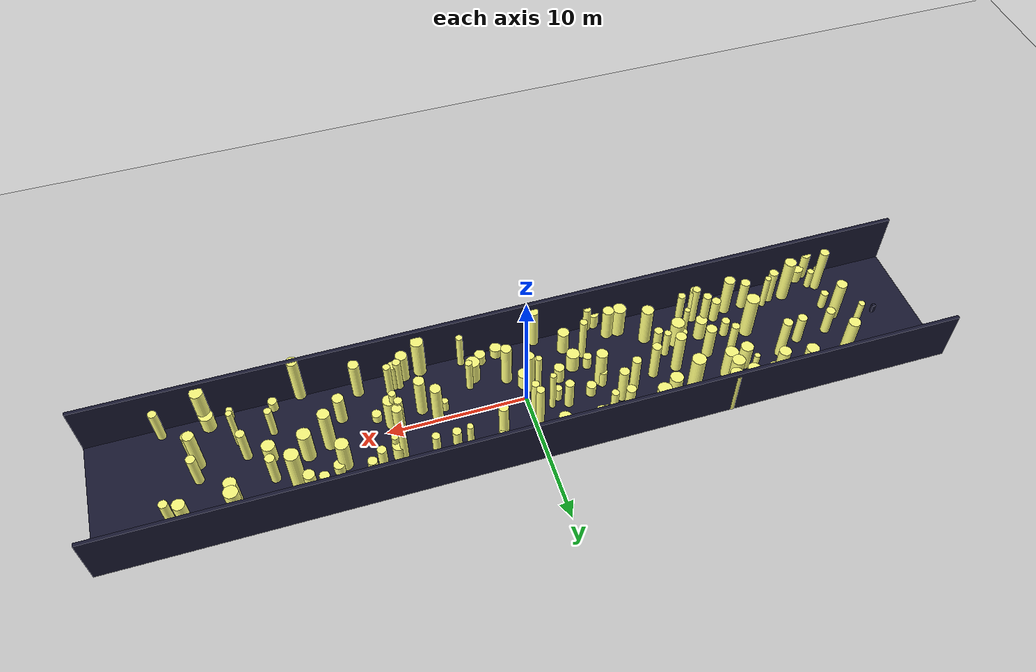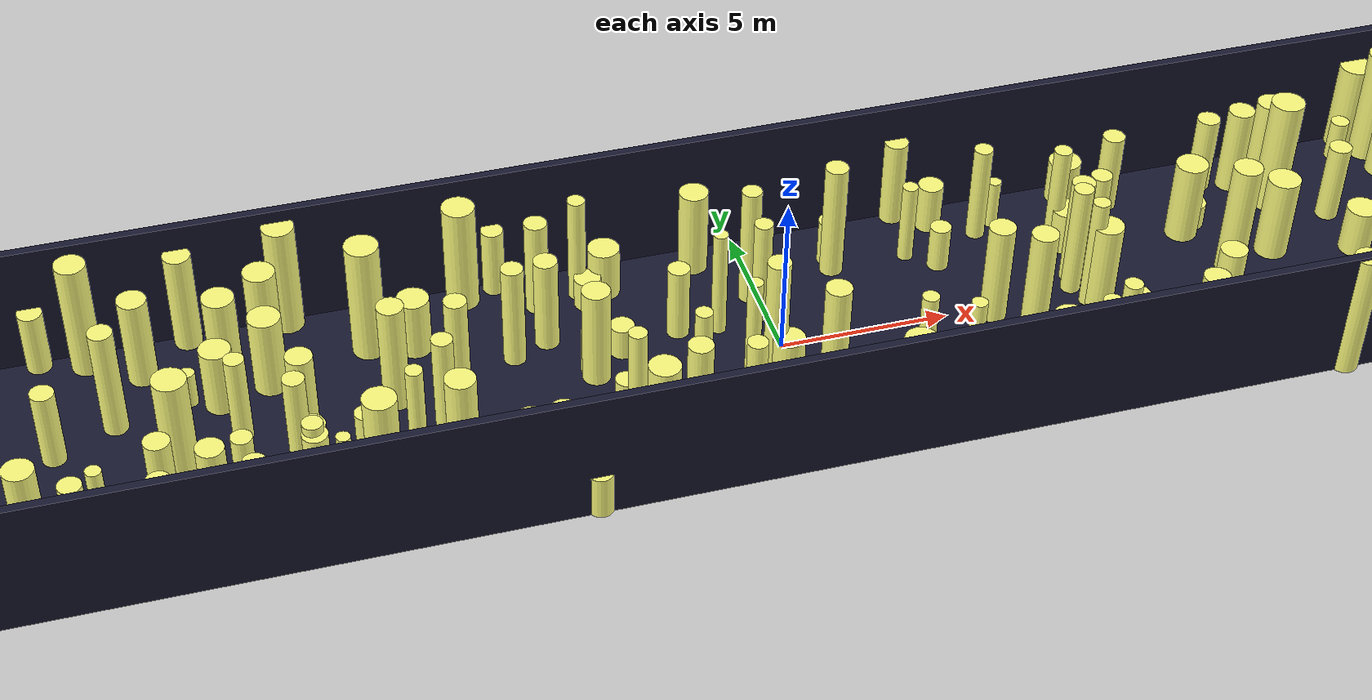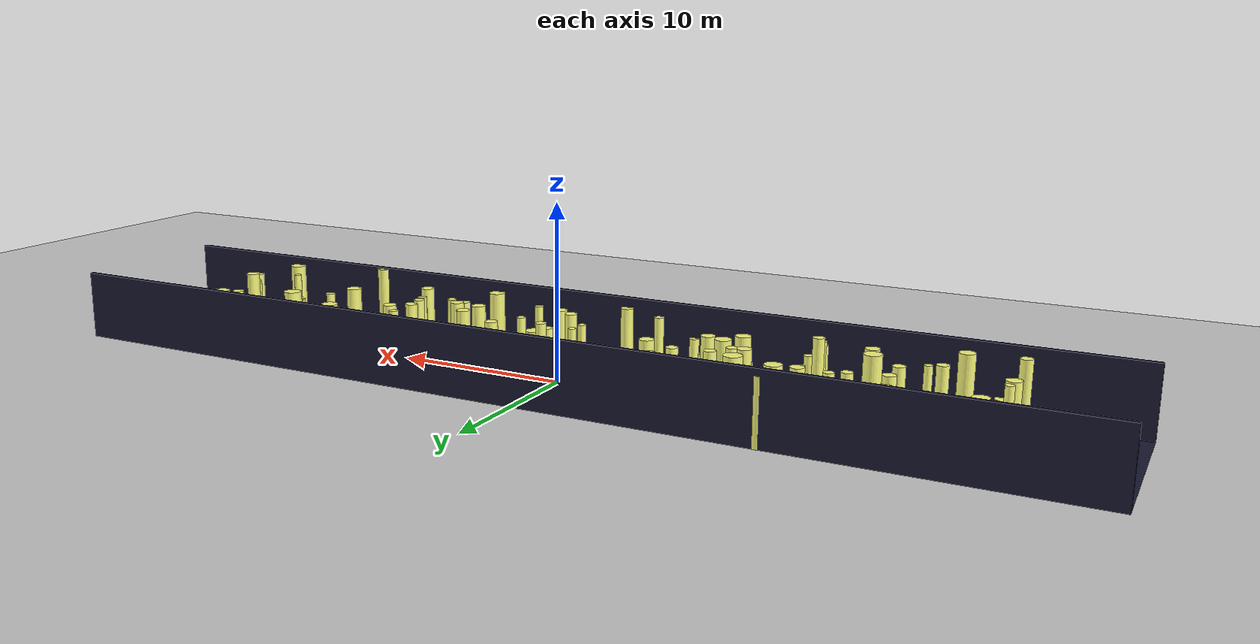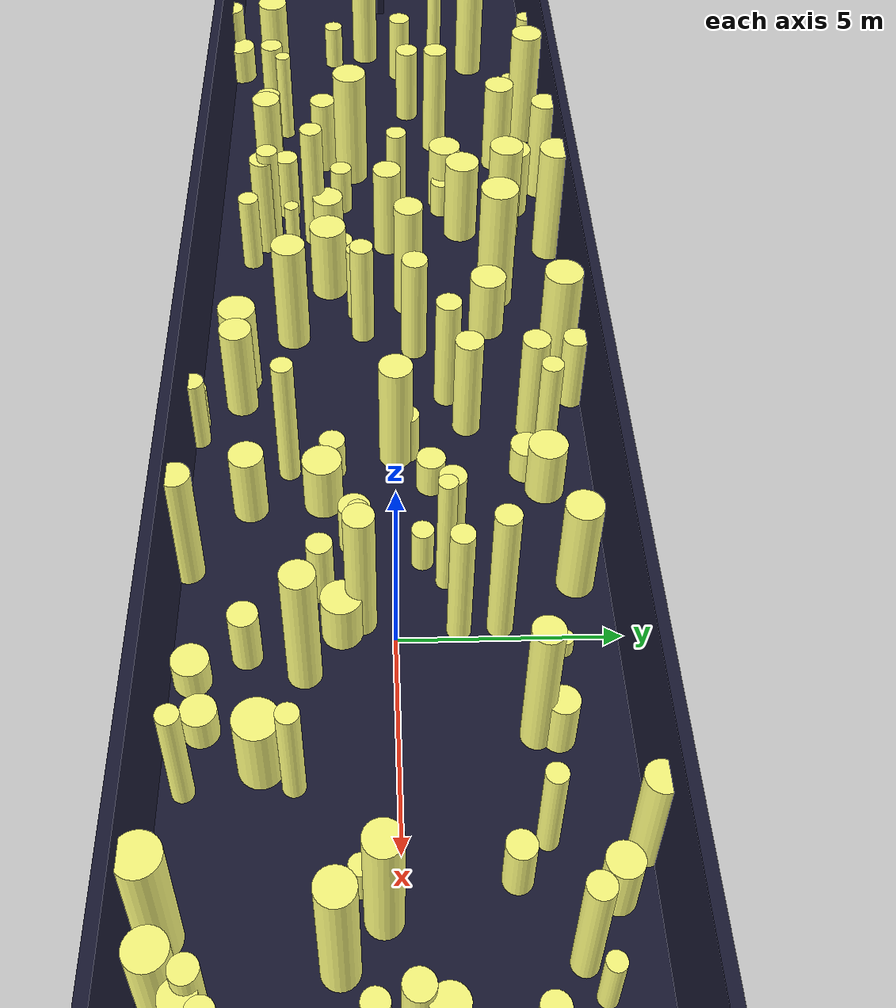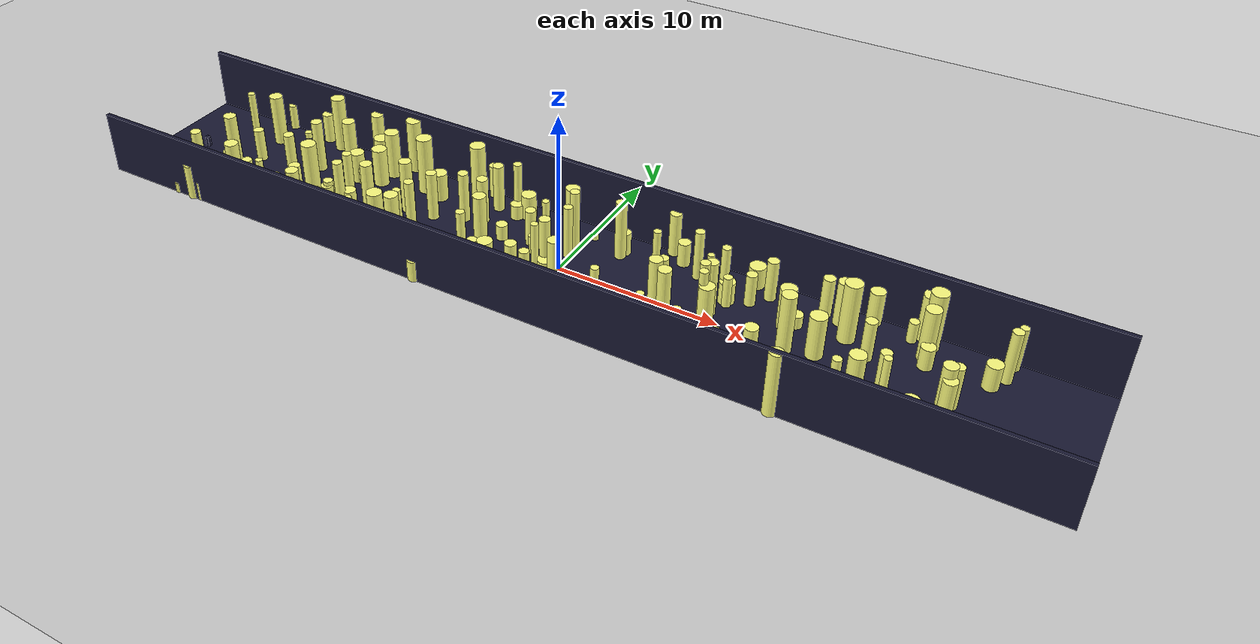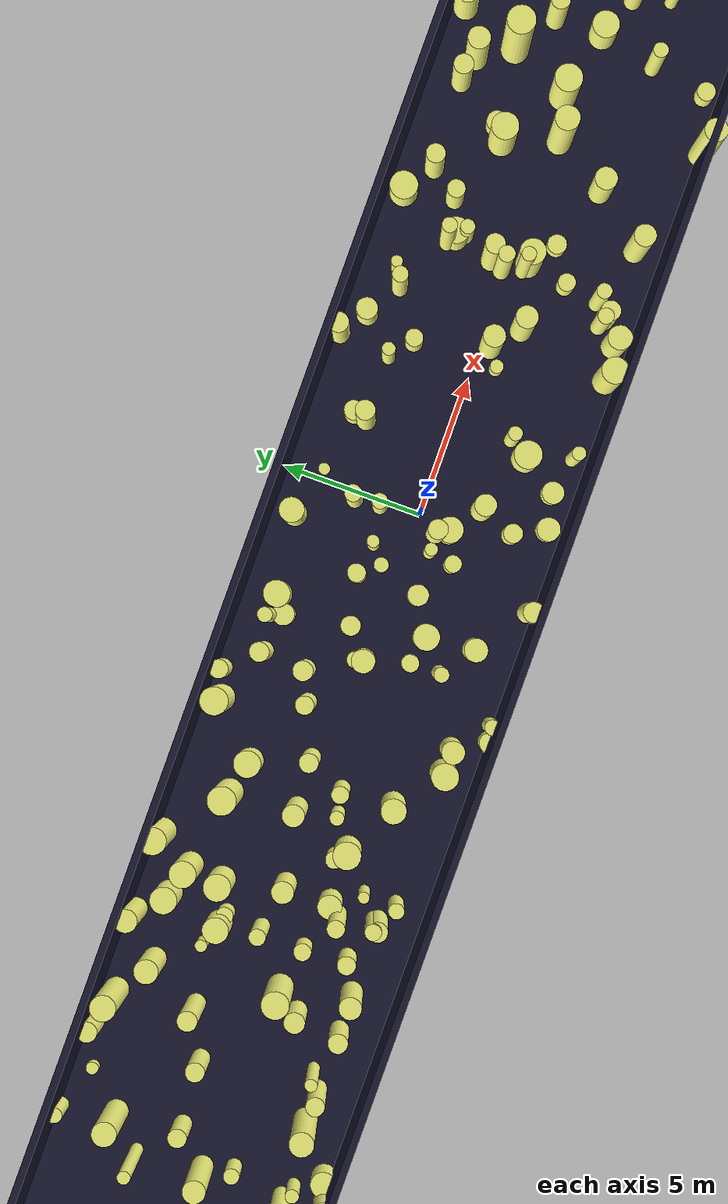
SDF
<?xml version="1.0"?>
<sdf version="1.4">
  <world name="default">
    <gui>
      <camera name="user_camera">
        <pose>-20 -30 40 0 0.66 0.83</pose>
      </camera>
    </gui>
    <include>
      <uri>model://ground_plane</uri>
    </include>
    <include>
      <uri>model://sun</uri>
    </include>
    <scene>
      <shadows>0</shadows>
    </scene>
    <model name="forest">
      <static>true</static>
      <link name="cylinder0">
        <pose>-0.27596573278064795 2.3027655550596826 1.9662998194130066 0 0 0 </pose>
        <visual name="visual">
          <geometry>
            <cylinder>
              <radius>0.29460365191055793</radius>
              <length>3.932599638826013</length>
            </cylinder>
          </geometry>
          <material>
            <ambient>0.6 0.6 0.6 1</ambient>
            <diffuse>1 1 0.5 1</diffuse>
            <specular>0 0 0</specular>
            <emissive>0 0 0 1</emissive>
          </material>
        </visual>
        <collision name="collision">
          <geometry>
            <cylinder>
              <radius>0.29460365191055793</radius>
              <length>3.932599638826013</length>
            </cylinder>
          </geometry>
          <max_contacts>0</max_contacts>
        </collision>
      </link>
      <link name="cylinder1">
        <pose>-13.425324815442846 4.684051941880119 1.8073464388554377 0 0 0 </pose>
        <visual name="visual">
          <geometry>
            <cylinder>
              <radius>0.4679928004351601</radius>
              <length>3.6146928777108753</length>
            </cylinder>
          </geometry>
          <material>
            <ambient>0.6 0.6 0.6 1</ambient>
            <diffuse>1 1 0.5 1</diffuse>
            <specular>0 0 0</specular>
            <emissive>0 0 0 1</emissive>
          </material>
        </visual>
        <collision name="collision">
          <geometry>
            <cylinder>
              <radius>0.4679928004351601</radius>
              <length>3.6146928777108753</length>
            </cylinder>
          </geometry>
          <max_contacts>0</max_contacts>
        </collision>
      </link>
      <link name="cylinder2">
        <pose>17.06263582477831 -4.398450498447433 0.45323441343859916 0 0 0 </pose>
        <visual name="visual">
          <geometry>
            <cylinder>
              <radius>0.327171497015727</radius>
              <length>0.9064688268771983</length>
            </cylinder>
          </geometry>
          <material>
            <ambient>0.6 0.6 0.6 1</ambient>
            <diffuse>1 1 0.5 1</diffuse>
            <specular>0 0 0</specular>
            <emissive>0 0 0 1</emissive>
          </material>
        </visual>
        <collision name="collision">
          <geometry>
            <cylinder>
              <radius>0.327171497015727</radius>
              <length>0.9064688268771983</length>
            </cylinder>
          </geometry>
          <max_contacts>0</max_contacts>
        </collision>
      </link>
      <link name="cylinder3">
        <pose>0.8533443847754789 -1.9828326244018832 1.7870015804718422 0 0 0 </pose>
        <visual name="visual">
          <geometry>
            <cylinder>
              <radius>0.378790075126895</radius>
              <length>3.5740031609436844</length>
            </cylinder>
          </geometry>
          <material>
            <ambient>0.6 0.6 0.6 1</ambient>
            <diffuse>1 1 0.5 1</diffuse>
            <specular>0 0 0</specular>
            <emissive>0 0 0 1</emissive>
          </material>
        </visual>
        <collision name="collision">
          <geometry>
            <cylinder>
              <radius>0.378790075126895</radius>
              <length>3.5740031609436844</length>
            </cylinder>
          </geometry>
          <max_contacts>0</max_contacts>
        </collision>
      </link>
      <link name="cylinder4">
        <pose>8.56006599126416 -3.777886421730795 1.21136380154914 0 0 0 </pose>
        <visual name="visual">
          <geometry>
            <cylinder>
              <radius>0.34854121331254384</radius>
              <length>2.42272760309828</length>
            </cylinder>
          </geometry>
          <material>
            <ambient>0.6 0.6 0.6 1</ambient>
            <diffuse>1 1 0.5 1</diffuse>
            <specular>0 0 0</specular>
            <emissive>0 0 0 1</emissive>
          </material>
        </visual>
        <collision name="collision">
          <geometry>
            <cylinder>
              <radius>0.34854121331254384</radius>
              <length>2.42272760309828</length>
            </cylinder>
          </geometry>
          <max_contacts>0</max_contacts>
        </collision>
      </link>
      <link name="cylinder5">
        <pose>21.548684478168738 -4.1583525839549775 0.7080071671654142 0 0 0 </pose>
        <visual name="visual">
          <geometry>
            <cylinder>
              <radius>0.49849775153081066</radius>
              <length>1.4160143343308285</length>
            </cylinder>
          </geometry>
          <material>
            <ambient>0.6 0.6 0.6 1</ambient>
            <diffuse>1 1 0.5 1</diffuse>
            <specular>0 0 0</specular>
            <emissive>0 0 0 1</emissive>
          </material>
        </visual>
        <collision name="collision">
          <geometry>
            <cylinder>
              <radius>0.49849775153081066</radius>
              <length>1.4160143343308285</length>
            </cylinder>
          </geometry>
          <max_contacts>0</max_contacts>
        </collision>
      </link>
      <link name="cylinder6">
        <pose>-23.200905450125763 2.9158026529113616 1.7294225878512632 0 0 0 </pose>
        <visual name="visual">
          <geometry>
            <cylinder>
              <radius>0.426228047189793</radius>
              <length>3.4588451757025265</length>
            </cylinder>
          </geometry>
          <material>
            <ambient>0.6 0.6 0.6 1</ambient>
            <diffuse>1 1 0.5 1</diffuse>
            <specular>0 0 0</specular>
            <emissive>0 0 0 1</emissive>
          </material>
        </visual>
        <collision name="collision">
          <geometry>
            <cylinder>
              <radius>0.426228047189793</radius>
              <length>3.4588451757025265</length>
            </cylinder>
          </geometry>
          <max_contacts>0</max_contacts>
        </collision>
      </link>
      <link name="cylinder7">
        <pose>10.398539037109742 4.321085919349361 0.7088886732083374 0 0 0 </pose>
        <visual name="visual">
          <geometry>
            <cylinder>
              <radius>0.4912446520581456</radius>
              <length>1.4177773464166747</length>
            </cylinder>
          </geometry>
          <material>
            <ambient>0.6 0.6 0.6 1</ambient>
            <diffuse>1 1 0.5 1</diffuse>
            <specular>0 0 0</specular>
            <emissive>0 0 0 1</emissive>
          </material>
        </visual>
        <collision name="collision">
          <geometry>
            <cylinder>
              <radius>0.4912446520581456</radius>
              <length>1.4177773464166747</length>
            </cylinder>
          </geometry>
          <max_contacts>0</max_contacts>
        </collision>
      </link>
      <link name="cylinder8">
        <pose>-20.079455899806838 -3.4347328216472315 1.4606840440277165 0 0 0 </pose>
        <visual name="visual">
          <geometry>
            <cylinder>
              <radius>0.32834331317839904</radius>
              <length>2.921368088055433</length>
            </cylinder>
          </geometry>
          <material>
            <ambient>0.6 0.6 0.6 1</ambient>
            <diffuse>1 1 0.5 1</diffuse>
            <specular>0 0 0</specular>
            <emissive>0 0 0 1</emissive>
          </material>
        </visual>
        <collision name="collision">
          <geometry>
            <cylinder>
              <radius>0.32834331317839904</radius>
              <length>2.921368088055433</length>
            </cylinder>
          </geometry>
          <max_contacts>0</max_contacts>
        </collision>
      </link>
      <link name="cylinder9">
        <pose>-16.298758542996715 4.6578932224588705 1.6140198769826912 0 0 0 </pose>
        <visual name="visual">
          <geometry>
            <cylinder>
              <radius>0.3998894027435421</radius>
              <length>3.2280397539653825</length>
            </cylinder>
          </geometry>
          <material>
            <ambient>0.6 0.6 0.6 1</ambient>
            <diffuse>1 1 0.5 1</diffuse>
            <specular>0 0 0</specular>
            <emissive>0 0 0 1</emissive>
          </material>
        </visual>
        <collision name="collision">
          <geometry>
            <cylinder>
              <radius>0.3998894027435421</radius>
              <length>3.2280397539653825</length>
            </cylinder>
          </geometry>
          <max_contacts>0</max_contacts>
        </collision>
      </link>
      <link name="cylinder10">
        <pose>-15.38589362293996 0.32492164306473637 1.4245857926261953 0 0 0 </pose>
        <visual name="visual">
          <geometry>
            <cylinder>
              <radius>0.2898272229201284</radius>
              <length>2.8491715852523907</length>
            </cylinder>
          </geometry>
          <material>
            <ambient>0.6 0.6 0.6 1</ambient>
            <diffuse>1 1 0.5 1</diffuse>
            <specular>0 0 0</specular>
            <emissive>0 0 0 1</emissive>
          </material>
        </visual>
        <collision name="collision">
          <geometry>
            <cylinder>
              <radius>0.2898272229201284</radius>
              <length>2.8491715852523907</length>
            </cylinder>
          </geometry>
          <max_contacts>0</max_contacts>
        </collision>
      </link>
      <link name="cylinder11">
        <pose>-20.50939731660361 4.701523323956634 1.0200462039419955 0 0 0 </pose>
        <visual name="visual">
          <geometry>
            <cylinder>
              <radius>0.3564871261405954</radius>
              <length>2.040092407883991</length>
            </cylinder>
          </geometry>
          <material>
            <ambient>0.6 0.6 0.6 1</ambient>
            <diffuse>1 1 0.5 1</diffuse>
            <specular>0 0 0</specular>
            <emissive>0 0 0 1</emissive>
          </material>
        </visual>
        <collision name="collision">
          <geometry>
            <cylinder>
              <radius>0.3564871261405954</radius>
              <length>2.040092407883991</length>
            </cylinder>
          </geometry>
          <max_contacts>0</max_contacts>
        </collision>
      </link>
      <link name="cylinder12">
        <pose>9.541805166291901 2.0957269221761967 0.7181970877184152 0 0 0 </pose>
        <visual name="visual">
          <geometry>
            <cylinder>
              <radius>0.46674660172449084</radius>
              <length>1.4363941754368303</length>
            </cylinder>
          </geometry>
          <material>
            <ambient>0.6 0.6 0.6 1</ambient>
            <diffuse>1 1 0.5 1</diffuse>
            <specular>0 0 0</specular>
            <emissive>0 0 0 1</emissive>
          </material>
        </visual>
        <collision name="collision">
          <geometry>
            <cylinder>
              <radius>0.46674660172449084</radius>
              <length>1.4363941754368303</length>
            </cylinder>
          </geometry>
          <max_contacts>0</max_contacts>
        </collision>
      </link>
      <link name="cylinder13">
        <pose>11.161338259415885 -3.963218649585535 1.6466238924237384 0 0 0 </pose>
        <visual name="visual">
          <geometry>
            <cylinder>
              <radius>0.3831152462688655</radius>
              <length>3.293247784847477</length>
            </cylinder>
          </geometry>
          <material>
            <ambient>0.6 0.6 0.6 1</ambient>
            <diffuse>1 1 0.5 1</diffuse>
            <specular>0 0 0</specular>
            <emissive>0 0 0 1</emissive>
          </material>
        </visual>
        <collision name="collision">
          <geometry>
            <cylinder>
              <radius>0.3831152462688655</radius>
              <length>3.293247784847477</length>
            </cylinder>
          </geometry>
          <max_contacts>0</max_contacts>
        </collision>
      </link>
      <link name="cylinder14">
        <pose>0.3872426090972496 -3.2432841573307405 0.8264207578981477 0 0 0 </pose>
        <visual name="visual">
          <geometry>
            <cylinder>
              <radius>0.3385856604099834</radius>
              <length>1.6528415157962955</length>
            </cylinder>
          </geometry>
          <material>
            <ambient>0.6 0.6 0.6 1</ambient>
            <diffuse>1 1 0.5 1</diffuse>
            <specular>0 0 0</specular>
            <emissive>0 0 0 1</emissive>
          </material>
        </visual>
        <collision name="collision">
          <geometry>
            <cylinder>
              <radius>0.3385856604099834</radius>
              <length>1.6528415157962955</length>
            </cylinder>
          </geometry>
          <max_contacts>0</max_contacts>
        </collision>
      </link>
      <link name="cylinder15">
        <pose>3.587341926778624 -4.363118269159628 1.4793409929411214 0 0 0 </pose>
        <visual name="visual">
          <geometry>
            <cylinder>
              <radius>0.24105849808572682</radius>
              <length>2.958681985882243</length>
            </cylinder>
          </geometry>
          <material>
            <ambient>0.6 0.6 0.6 1</ambient>
            <diffuse>1 1 0.5 1</diffuse>
            <specular>0 0 0</specular>
            <emissive>0 0 0 1</emissive>
          </material>
        </visual>
        <collision name="collision">
          <geometry>
            <cylinder>
              <radius>0.24105849808572682</radius>
              <length>2.958681985882243</length>
            </cylinder>
          </geometry>
          <max_contacts>0</max_contacts>
        </collision>
      </link>
      <link name="cylinder16">
        <pose>-15.3302228265768 1.6473909878124022 0.577696933725347 0 0 0 </pose>
        <visual name="visual">
          <geometry>
            <cylinder>
              <radius>0.29862722217275395</radius>
              <length>1.155393867450694</length>
            </cylinder>
          </geometry>
          <material>
            <ambient>0.6 0.6 0.6 1</ambient>
            <diffuse>1 1 0.5 1</diffuse>
            <specular>0 0 0</specular>
            <emissive>0 0 0 1</emissive>
          </material>
        </visual>
        <collision name="collision">
          <geometry>
            <cylinder>
              <radius>0.29862722217275395</radius>
              <length>1.155393867450694</length>
            </cylinder>
          </geometry>
          <max_contacts>0</max_contacts>
        </collision>
      </link>
      <link name="cylinder17">
        <pose>-12.206962141053667 -1.255467921592385 0.7657628428371847 0 0 0 </pose>
        <visual name="visual">
          <geometry>
            <cylinder>
              <radius>0.30896001584463373</radius>
              <length>1.5315256856743693</length>
            </cylinder>
          </geometry>
          <material>
            <ambient>0.6 0.6 0.6 1</ambient>
            <diffuse>1 1 0.5 1</diffuse>
            <specular>0 0 0</specular>
            <emissive>0 0 0 1</emissive>
          </material>
        </visual>
        <collision name="collision">
          <geometry>
            <cylinder>
              <radius>0.30896001584463373</radius>
              <length>1.5315256856743693</length>
            </cylinder>
          </geometry>
          <max_contacts>0</max_contacts>
        </collision>
      </link>
      <link name="cylinder18">
        <pose>9.46966332199478 -0.6176820948401032 1.437163118635355 0 0 0 </pose>
        <visual name="visual">
          <geometry>
            <cylinder>
              <radius>0.44921465185849613</radius>
              <length>2.87432623727071</length>
            </cylinder>
          </geometry>
          <material>
            <ambient>0.6 0.6 0.6 1</ambient>
            <diffuse>1 1 0.5 1</diffuse>
            <specular>0 0 0</specular>
            <emissive>0 0 0 1</emissive>
          </material>
        </visual>
        <collision name="collision">
          <geometry>
            <cylinder>
              <radius>0.44921465185849613</radius>
              <length>2.87432623727071</length>
            </cylinder>
          </geometry>
          <max_contacts>0</max_contacts>
        </collision>
      </link>
      <link name="cylinder19">
        <pose>-24.216951786448693 1.7955132381273398 1.9396257549318858 0 0 0 </pose>
        <visual name="visual">
          <geometry>
            <cylinder>
              <radius>0.2291035028655035</radius>
              <length>3.8792515098637717</length>
            </cylinder>
          </geometry>
          <material>
            <ambient>0.6 0.6 0.6 1</ambient>
            <diffuse>1 1 0.5 1</diffuse>
            <specular>0 0 0</specular>
            <emissive>0 0 0 1</emissive>
          </material>
        </visual>
        <collision name="collision">
          <geometry>
            <cylinder>
              <radius>0.2291035028655035</radius>
              <length>3.8792515098637717</length>
            </cylinder>
          </geometry>
          <max_contacts>0</max_contacts>
        </collision>
      </link>
      <link name="cylinder20">
        <pose>-6.313498661550838 3.49514028535104 1.575735215364361 0 0 0 </pose>
        <visual name="visual">
          <geometry>
            <cylinder>
              <radius>0.3395512921505083</radius>
              <length>3.151470430728722</length>
            </cylinder>
          </geometry>
          <material>
            <ambient>0.6 0.6 0.6 1</ambient>
            <diffuse>1 1 0.5 1</diffuse>
            <specular>0 0 0</specular>
            <emissive>0 0 0 1</emissive>
          </material>
        </visual>
        <collision name="collision">
          <geometry>
            <cylinder>
              <radius>0.3395512921505083</radius>
              <length>3.151470430728722</length>
            </cylinder>
          </geometry>
          <max_contacts>0</max_contacts>
        </collision>
      </link>
      <link name="cylinder21">
        <pose>24.766122047103792 -4.314615456266133 1.3455922960052131 0 0 0 </pose>
        <visual name="visual">
          <geometry>
            <cylinder>
              <radius>0.3020595572088285</radius>
              <length>2.6911845920104263</length>
            </cylinder>
          </geometry>
          <material>
            <ambient>0.6 0.6 0.6 1</ambient>
            <diffuse>1 1 0.5 1</diffuse>
            <specular>0 0 0</specular>
            <emissive>0 0 0 1</emissive>
          </material>
        </visual>
        <collision name="collision">
          <geometry>
            <cylinder>
              <radius>0.3020595572088285</radius>
              <length>2.6911845920104263</length>
            </cylinder>
          </geometry>
          <max_contacts>0</max_contacts>
        </collision>
      </link>
      <link name="cylinder22">
        <pose>-5.431169609507229 0.10766228422718438 1.596106110423506 0 0 0 </pose>
        <visual name="visual">
          <geometry>
            <cylinder>
              <radius>0.4094059961450005</radius>
              <length>3.192212220847012</length>
            </cylinder>
          </geometry>
          <material>
            <ambient>0.6 0.6 0.6 1</ambient>
            <diffuse>1 1 0.5 1</diffuse>
            <specular>0 0 0</specular>
            <emissive>0 0 0 1</emissive>
          </material>
        </visual>
        <collision name="collision">
          <geometry>
            <cylinder>
              <radius>0.4094059961450005</radius>
              <length>3.192212220847012</length>
            </cylinder>
          </geometry>
          <max_contacts>0</max_contacts>
        </collision>
      </link>
      <link name="cylinder23">
        <pose>7.789420767503266 -4.3731671185979435 1.2543017956717983 0 0 0 </pose>
        <visual name="visual">
          <geometry>
            <cylinder>
              <radius>0.42235897343363227</radius>
              <length>2.5086035913435967</length>
            </cylinder>
          </geometry>
          <material>
            <ambient>0.6 0.6 0.6 1</ambient>
            <diffuse>1 1 0.5 1</diffuse>
            <specular>0 0 0</specular>
            <emissive>0 0 0 1</emissive>
          </material>
        </visual>
        <collision name="collision">
          <geometry>
            <cylinder>
              <radius>0.42235897343363227</radius>
              <length>2.5086035913435967</length>
            </cylinder>
          </geometry>
          <max_contacts>0</max_contacts>
        </collision>
      </link>
      <link name="cylinder24">
        <pose>3.5151456912194554 -2.1303041103750955 1.3997497912851216 0 0 0 </pose>
        <visual name="visual">
          <geometry>
            <cylinder>
              <radius>0.24697764225073554</radius>
              <length>2.799499582570243</length>
            </cylinder>
          </geometry>
          <material>
            <ambient>0.6 0.6 0.6 1</ambient>
            <diffuse>1 1 0.5 1</diffuse>
            <specular>0 0 0</specular>
            <emissive>0 0 0 1</emissive>
          </material>
        </visual>
        <collision name="collision">
          <geometry>
            <cylinder>
              <radius>0.24697764225073554</radius>
              <length>2.799499582570243</length>
            </cylinder>
          </geometry>
          <max_contacts>0</max_contacts>
        </collision>
      </link>
      <link name="cylinder25">
        <pose>-23.622724659389142 -1.602220369215365 0.7410076853481786 0 0 0 </pose>
        <visual name="visual">
          <geometry>
            <cylinder>
              <radius>0.2824663787287972</radius>
              <length>1.4820153706963572</length>
            </cylinder>
          </geometry>
          <material>
            <ambient>0.6 0.6 0.6 1</ambient>
            <diffuse>1 1 0.5 1</diffuse>
            <specular>0 0 0</specular>
            <emissive>0 0 0 1</emissive>
          </material>
        </visual>
        <collision name="collision">
          <geometry>
            <cylinder>
              <radius>0.2824663787287972</radius>
              <length>1.4820153706963572</length>
            </cylinder>
          </geometry>
          <max_contacts>0</max_contacts>
        </collision>
      </link>
      <link name="cylinder26">
        <pose>7.193458350136424 3.3149631198163227 1.6025751114651041 0 0 0 </pose>
        <visual name="visual">
          <geometry>
            <cylinder>
              <radius>0.278477207770003</radius>
              <length>3.2051502229302082</length>
            </cylinder>
          </geometry>
          <material>
            <ambient>0.6 0.6 0.6 1</ambient>
            <diffuse>1 1 0.5 1</diffuse>
            <specular>0 0 0</specular>
            <emissive>0 0 0 1</emissive>
          </material>
        </visual>
        <collision name="collision">
          <geometry>
            <cylinder>
              <radius>0.278477207770003</radius>
              <length>3.2051502229302082</length>
            </cylinder>
          </geometry>
          <max_contacts>0</max_contacts>
        </collision>
      </link>
      <link name="cylinder27">
        <pose>-17.728571144775824 3.4578591734937145 1.4523116424741584 0 0 0 </pose>
        <visual name="visual">
          <geometry>
            <cylinder>
              <radius>0.42085033968195645</radius>
              <length>2.904623284948317</length>
            </cylinder>
          </geometry>
          <material>
            <ambient>0.6 0.6 0.6 1</ambient>
            <diffuse>1 1 0.5 1</diffuse>
            <specular>0 0 0</specular>
            <emissive>0 0 0 1</emissive>
          </material>
        </visual>
        <collision name="collision">
          <geometry>
            <cylinder>
              <radius>0.42085033968195645</radius>
              <length>2.904623284948317</length>
            </cylinder>
          </geometry>
          <max_contacts>0</max_contacts>
        </collision>
      </link>
      <link name="cylinder28">
        <pose>-5.5113321428176825 0.3849030072967752 0.7422895267263347 0 0 0 </pose>
        <visual name="visual">
          <geometry>
            <cylinder>
              <radius>0.2962670421375333</radius>
              <length>1.4845790534526695</length>
            </cylinder>
          </geometry>
          <material>
            <ambient>0.6 0.6 0.6 1</ambient>
            <diffuse>1 1 0.5 1</diffuse>
            <specular>0 0 0</specular>
            <emissive>0 0 0 1</emissive>
          </material>
        </visual>
        <collision name="collision">
          <geometry>
            <cylinder>
              <radius>0.2962670421375333</radius>
              <length>1.4845790534526695</length>
            </cylinder>
          </geometry>
          <max_contacts>0</max_contacts>
        </collision>
      </link>
      <link name="cylinder29">
        <pose>4.782275414142273 2.8620519904918442 1.3210972901681837 0 0 0 </pose>
        <visual name="visual">
          <geometry>
            <cylinder>
              <radius>0.2303400498323811</radius>
              <length>2.6421945803363673</length>
            </cylinder>
          </geometry>
          <material>
            <ambient>0.6 0.6 0.6 1</ambient>
            <diffuse>1 1 0.5 1</diffuse>
            <specular>0 0 0</specular>
            <emissive>0 0 0 1</emissive>
          </material>
        </visual>
        <collision name="collision">
          <geometry>
            <cylinder>
              <radius>0.2303400498323811</radius>
              <length>2.6421945803363673</length>
            </cylinder>
          </geometry>
          <max_contacts>0</max_contacts>
        </collision>
      </link>
      <link name="cylinder30">
        <pose>-6.090910868536813 -4.7910375395340035 1.0784188501266392 0 0 0 </pose>
        <visual name="visual">
          <geometry>
            <cylinder>
              <radius>0.27294622840925337</radius>
              <length>2.1568377002532784</length>
            </cylinder>
          </geometry>
          <material>
            <ambient>0.6 0.6 0.6 1</ambient>
            <diffuse>1 1 0.5 1</diffuse>
            <specular>0 0 0</specular>
            <emissive>0 0 0 1</emissive>
          </material>
        </visual>
        <collision name="collision">
          <geometry>
            <cylinder>
              <radius>0.27294622840925337</radius>
              <length>2.1568377002532784</length>
            </cylinder>
          </geometry>
          <max_contacts>0</max_contacts>
        </collision>
      </link>
      <link name="cylinder31">
        <pose>-4.2766366844724395 3.679652418486711 0.8334056321843029 0 0 0 </pose>
        <visual name="visual">
          <geometry>
            <cylinder>
              <radius>0.4705615520282012</radius>
              <length>1.6668112643686057</length>
            </cylinder>
          </geometry>
          <material>
            <ambient>0.6 0.6 0.6 1</ambient>
            <diffuse>1 1 0.5 1</diffuse>
            <specular>0 0 0</specular>
            <emissive>0 0 0 1</emissive>
          </material>
        </visual>
        <collision name="collision">
          <geometry>
            <cylinder>
              <radius>0.4705615520282012</radius>
              <length>1.6668112643686057</length>
            </cylinder>
          </geometry>
          <max_contacts>0</max_contacts>
        </collision>
      </link>
      <link name="cylinder32">
        <pose>-21.978491770533545 4.20373646093549 0.23649092039902228 0 0 0 </pose>
        <visual name="visual">
          <geometry>
            <cylinder>
              <radius>0.222380991836974</radius>
              <length>0.47298184079804456</length>
            </cylinder>
          </geometry>
          <material>
            <ambient>0.6 0.6 0.6 1</ambient>
            <diffuse>1 1 0.5 1</diffuse>
            <specular>0 0 0</specular>
            <emissive>0 0 0 1</emissive>
          </material>
        </visual>
        <collision name="collision">
          <geometry>
            <cylinder>
              <radius>0.222380991836974</radius>
              <length>0.47298184079804456</length>
            </cylinder>
          </geometry>
          <max_contacts>0</max_contacts>
        </collision>
      </link>
      <link name="cylinder33">
        <pose>-23.621865823111143 4.806129667702864 0.8817907112433951 0 0 0 </pose>
        <visual name="visual">
          <geometry>
            <cylinder>
              <radius>0.2700935335505821</radius>
              <length>1.7635814224867903</length>
            </cylinder>
          </geometry>
          <material>
            <ambient>0.6 0.6 0.6 1</ambient>
            <diffuse>1 1 0.5 1</diffuse>
            <specular>0 0 0</specular>
            <emissive>0 0 0 1</emissive>
          </material>
        </visual>
        <collision name="collision">
          <geometry>
            <cylinder>
              <radius>0.2700935335505821</radius>
              <length>1.7635814224867903</length>
            </cylinder>
          </geometry>
          <max_contacts>0</max_contacts>
        </collision>
      </link>
      <link name="cylinder34">
        <pose>15.107928935892687 -4.964952932846998 1.9565724542738754 0 0 0 </pose>
        <visual name="visual">
          <geometry>
            <cylinder>
              <radius>0.3967756741619876</radius>
              <length>3.9131449085477508</length>
            </cylinder>
          </geometry>
          <material>
            <ambient>0.6 0.6 0.6 1</ambient>
            <diffuse>1 1 0.5 1</diffuse>
            <specular>0 0 0</specular>
            <emissive>0 0 0 1</emissive>
          </material>
        </visual>
        <collision name="collision">
          <geometry>
            <cylinder>
              <radius>0.3967756741619876</radius>
              <length>3.9131449085477508</length>
            </cylinder>
          </geometry>
          <max_contacts>0</max_contacts>
        </collision>
      </link>
      <link name="cylinder35">
        <pose>12.706050622001463 -2.1137591758437955 1.2374132726244835 0 0 0 </pose>
        <visual name="visual">
          <geometry>
            <cylinder>
              <radius>0.3934762514498227</radius>
              <length>2.474826545248967</length>
            </cylinder>
          </geometry>
          <material>
            <ambient>0.6 0.6 0.6 1</ambient>
            <diffuse>1 1 0.5 1</diffuse>
            <specular>0 0 0</specular>
            <emissive>0 0 0 1</emissive>
          </material>
        </visual>
        <collision name="collision">
          <geometry>
            <cylinder>
              <radius>0.3934762514498227</radius>
              <length>2.474826545248967</length>
            </cylinder>
          </geometry>
          <max_contacts>0</max_contacts>
        </collision>
      </link>
      <link name="cylinder36">
        <pose>9.197053254391541 -0.5105110384902511 1.8381948339444554 0 0 0 </pose>
        <visual name="visual">
          <geometry>
            <cylinder>
              <radius>0.24995701619388372</radius>
              <length>3.6763896678889108</length>
            </cylinder>
          </geometry>
          <material>
            <ambient>0.6 0.6 0.6 1</ambient>
            <diffuse>1 1 0.5 1</diffuse>
            <specular>0 0 0</specular>
            <emissive>0 0 0 1</emissive>
          </material>
        </visual>
        <collision name="collision">
          <geometry>
            <cylinder>
              <radius>0.24995701619388372</radius>
              <length>3.6763896678889108</length>
            </cylinder>
          </geometry>
          <max_contacts>0</max_contacts>
        </collision>
      </link>
      <link name="cylinder37">
        <pose>2.22098658588315 -4.09902437544424 0.4561334338542336 0 0 0 </pose>
        <visual name="visual">
          <geometry>
            <cylinder>
              <radius>0.39335598329948684</radius>
              <length>0.9122668677084672</length>
            </cylinder>
          </geometry>
          <material>
            <ambient>0.6 0.6 0.6 1</ambient>
            <diffuse>1 1 0.5 1</diffuse>
            <specular>0 0 0</specular>
            <emissive>0 0 0 1</emissive>
          </material>
        </visual>
        <collision name="collision">
          <geometry>
            <cylinder>
              <radius>0.39335598329948684</radius>
              <length>0.9122668677084672</length>
            </cylinder>
          </geometry>
          <max_contacts>0</max_contacts>
        </collision>
      </link>
      <link name="cylinder38">
        <pose>-1.9714821560423879 -4.702370178172775 1.7159752581711314 0 0 0 </pose>
        <visual name="visual">
          <geometry>
            <cylinder>
              <radius>0.3573550583101269</radius>
              <length>3.431950516342263</length>
            </cylinder>
          </geometry>
          <material>
            <ambient>0.6 0.6 0.6 1</ambient>
            <diffuse>1 1 0.5 1</diffuse>
            <specular>0 0 0</specular>
            <emissive>0 0 0 1</emissive>
          </material>
        </visual>
        <collision name="collision">
          <geometry>
            <cylinder>
              <radius>0.3573550583101269</radius>
              <length>3.431950516342263</length>
            </cylinder>
          </geometry>
          <max_contacts>0</max_contacts>
        </collision>
      </link>
      <link name="cylinder39">
        <pose>-23.521100365539365 -4.924859397098956 1.1373021459224835 0 0 0 </pose>
        <visual name="visual">
          <geometry>
            <cylinder>
              <radius>0.3732747650827203</radius>
              <length>2.274604291844967</length>
            </cylinder>
          </geometry>
          <material>
            <ambient>0.6 0.6 0.6 1</ambient>
            <diffuse>1 1 0.5 1</diffuse>
            <specular>0 0 0</specular>
            <emissive>0 0 0 1</emissive>
          </material>
        </visual>
        <collision name="collision">
          <geometry>
            <cylinder>
              <radius>0.3732747650827203</radius>
              <length>2.274604291844967</length>
            </cylinder>
          </geometry>
          <max_contacts>0</max_contacts>
        </collision>
      </link>
      <link name="cylinder40">
        <pose>-3.8046622959511396 -3.3842398450957125 1.008785948485795 0 0 0 </pose>
        <visual name="visual">
          <geometry>
            <cylinder>
              <radius>0.4147580997780579</radius>
              <length>2.01757189697159</length>
            </cylinder>
          </geometry>
          <material>
            <ambient>0.6 0.6 0.6 1</ambient>
            <diffuse>1 1 0.5 1</diffuse>
            <specular>0 0 0</specular>
            <emissive>0 0 0 1</emissive>
          </material>
        </visual>
        <collision name="collision">
          <geometry>
            <cylinder>
              <radius>0.4147580997780579</radius>
              <length>2.01757189697159</length>
            </cylinder>
          </geometry>
          <max_contacts>0</max_contacts>
        </collision>
      </link>
      <link name="cylinder41">
        <pose>-11.057983642045416 0.557611453082921 1.7652778801738367 0 0 0 </pose>
        <visual name="visual">
          <geometry>
            <cylinder>
              <radius>0.38303141651306294</radius>
              <length>3.5305557603476734</length>
            </cylinder>
          </geometry>
          <material>
            <ambient>0.6 0.6 0.6 1</ambient>
            <diffuse>1 1 0.5 1</diffuse>
            <specular>0 0 0</specular>
            <emissive>0 0 0 1</emissive>
          </material>
        </visual>
        <collision name="collision">
          <geometry>
            <cylinder>
              <radius>0.38303141651306294</radius>
              <length>3.5305557603476734</length>
            </cylinder>
          </geometry>
          <max_contacts>0</max_contacts>
        </collision>
      </link>
      <link name="cylinder42">
        <pose>-4.963759250998667 -2.4985493442247964 1.8681536193753285 0 0 0 </pose>
        <visual name="visual">
          <geometry>
            <cylinder>
              <radius>0.2618273209065501</radius>
              <length>3.736307238750657</length>
            </cylinder>
          </geometry>
          <material>
            <ambient>0.6 0.6 0.6 1</ambient>
            <diffuse>1 1 0.5 1</diffuse>
            <specular>0 0 0</specular>
            <emissive>0 0 0 1</emissive>
          </material>
        </visual>
        <collision name="collision">
          <geometry>
            <cylinder>
              <radius>0.2618273209065501</radius>
              <length>3.736307238750657</length>
            </cylinder>
          </geometry>
          <max_contacts>0</max_contacts>
        </collision>
      </link>
      <link name="cylinder43">
        <pose>-13.041577894233514 -3.8120170278104326 1.181280168577643 0 0 0 </pose>
        <visual name="visual">
          <geometry>
            <cylinder>
              <radius>0.2761269920473245</radius>
              <length>2.362560337155286</length>
            </cylinder>
          </geometry>
          <material>
            <ambient>0.6 0.6 0.6 1</ambient>
            <diffuse>1 1 0.5 1</diffuse>
            <specular>0 0 0</specular>
            <emissive>0 0 0 1</emissive>
          </material>
        </visual>
        <collision name="collision">
          <geometry>
            <cylinder>
              <radius>0.2761269920473245</radius>
              <length>2.362560337155286</length>
            </cylinder>
          </geometry>
          <max_contacts>0</max_contacts>
        </collision>
      </link>
      <link name="cylinder44">
        <pose>8.263156415661705 -3.660597588238288 1.413286338722604 0 0 0 </pose>
        <visual name="visual">
          <geometry>
            <cylinder>
              <radius>0.2786597882645635</radius>
              <length>2.826572677445208</length>
            </cylinder>
          </geometry>
          <material>
            <ambient>0.6 0.6 0.6 1</ambient>
            <diffuse>1 1 0.5 1</diffuse>
            <specular>0 0 0</specular>
            <emissive>0 0 0 1</emissive>
          </material>
        </visual>
        <collision name="collision">
          <geometry>
            <cylinder>
              <radius>0.2786597882645635</radius>
              <length>2.826572677445208</length>
            </cylinder>
          </geometry>
          <max_contacts>0</max_contacts>
        </collision>
      </link>
      <link name="cylinder45">
        <pose>-13.818642532087095 -3.416232823194172 1.555280692205452 0 0 0 </pose>
        <visual name="visual">
          <geometry>
            <cylinder>
              <radius>0.3525645860288691</radius>
              <length>3.110561384410904</length>
            </cylinder>
          </geometry>
          <material>
            <ambient>0.6 0.6 0.6 1</ambient>
            <diffuse>1 1 0.5 1</diffuse>
            <specular>0 0 0</specular>
            <emissive>0 0 0 1</emissive>
          </material>
        </visual>
        <collision name="collision">
          <geometry>
            <cylinder>
              <radius>0.3525645860288691</radius>
              <length>3.110561384410904</length>
            </cylinder>
          </geometry>
          <max_contacts>0</max_contacts>
        </collision>
      </link>
      <link name="cylinder46">
        <pose>-7.345873493882234 4.64371863540881 1.11434148683003 0 0 0 </pose>
        <visual name="visual">
          <geometry>
            <cylinder>
              <radius>0.32942431847453313</radius>
              <length>2.22868297366006</length>
            </cylinder>
          </geometry>
          <material>
            <ambient>0.6 0.6 0.6 1</ambient>
            <diffuse>1 1 0.5 1</diffuse>
            <specular>0 0 0</specular>
            <emissive>0 0 0 1</emissive>
          </material>
        </visual>
        <collision name="collision">
          <geometry>
            <cylinder>
              <radius>0.32942431847453313</radius>
              <length>2.22868297366006</length>
            </cylinder>
          </geometry>
          <max_contacts>0</max_contacts>
        </collision>
      </link>
      <link name="cylinder47">
        <pose>-5.061527315618932 3.721935583270472 1.7645251837878395 0 0 0 </pose>
        <visual name="visual">
          <geometry>
            <cylinder>
              <radius>0.25947089892545744</radius>
              <length>3.529050367575679</length>
            </cylinder>
          </geometry>
          <material>
            <ambient>0.6 0.6 0.6 1</ambient>
            <diffuse>1 1 0.5 1</diffuse>
            <specular>0 0 0</specular>
            <emissive>0 0 0 1</emissive>
          </material>
        </visual>
        <collision name="collision">
          <geometry>
            <cylinder>
              <radius>0.25947089892545744</radius>
              <length>3.529050367575679</length>
            </cylinder>
          </geometry>
          <max_contacts>0</max_contacts>
        </collision>
      </link>
      <link name="cylinder48">
        <pose>-1.5438663993116926 1.1455206450608069 1.765208912737388 0 0 0 </pose>
        <visual name="visual">
          <geometry>
            <cylinder>
              <radius>0.21610772324643698</radius>
              <length>3.530417825474776</length>
            </cylinder>
          </geometry>
          <material>
            <ambient>0.6 0.6 0.6 1</ambient>
            <diffuse>1 1 0.5 1</diffuse>
            <specular>0 0 0</specular>
            <emissive>0 0 0 1</emissive>
          </material>
        </visual>
        <collision name="collision">
          <geometry>
            <cylinder>
              <radius>0.21610772324643698</radius>
              <length>3.530417825474776</length>
            </cylinder>
          </geometry>
          <max_contacts>0</max_contacts>
        </collision>
      </link>
      <link name="cylinder49">
        <pose>24.801665515858105 4.49977297706133 1.3858517608997916 0 0 0 </pose>
        <visual name="visual">
          <geometry>
            <cylinder>
              <radius>0.2472381237248637</radius>
              <length>2.771703521799583</length>
            </cylinder>
          </geometry>
          <material>
            <ambient>0.6 0.6 0.6 1</ambient>
            <diffuse>1 1 0.5 1</diffuse>
            <specular>0 0 0</specular>
            <emissive>0 0 0 1</emissive>
          </material>
        </visual>
        <collision name="collision">
          <geometry>
            <cylinder>
              <radius>0.2472381237248637</radius>
              <length>2.771703521799583</length>
            </cylinder>
          </geometry>
          <max_contacts>0</max_contacts>
        </collision>
      </link>
      <link name="cylinder50">
        <pose>-17.1818574459802 -1.0047567842385008 1.848393053407458 0 0 0 </pose>
        <visual name="visual">
          <geometry>
            <cylinder>
              <radius>0.47713528465152427</radius>
              <length>3.696786106814916</length>
            </cylinder>
          </geometry>
          <material>
            <ambient>0.6 0.6 0.6 1</ambient>
            <diffuse>1 1 0.5 1</diffuse>
            <specular>0 0 0</specular>
            <emissive>0 0 0 1</emissive>
          </material>
        </visual>
        <collision name="collision">
          <geometry>
            <cylinder>
              <radius>0.47713528465152427</radius>
              <length>3.696786106814916</length>
            </cylinder>
          </geometry>
          <max_contacts>0</max_contacts>
        </collision>
      </link>
      <link name="cylinder51">
        <pose>-11.850265373017328 -1.6032519020101321 1.1351853709411586 0 0 0 </pose>
        <visual name="visual">
          <geometry>
            <cylinder>
              <radius>0.4878930821655726</radius>
              <length>2.270370741882317</length>
            </cylinder>
          </geometry>
          <material>
            <ambient>0.6 0.6 0.6 1</ambient>
            <diffuse>1 1 0.5 1</diffuse>
            <specular>0 0 0</specular>
            <emissive>0 0 0 1</emissive>
          </material>
        </visual>
        <collision name="collision">
          <geometry>
            <cylinder>
              <radius>0.4878930821655726</radius>
              <length>2.270370741882317</length>
            </cylinder>
          </geometry>
          <max_contacts>0</max_contacts>
        </collision>
      </link>
      <link name="cylinder52">
        <pose>21.650200436551422 -4.555256958221218 1.7613387658371924 0 0 0 </pose>
        <visual name="visual">
          <geometry>
            <cylinder>
              <radius>0.4658754994408512</radius>
              <length>3.522677531674385</length>
            </cylinder>
          </geometry>
          <material>
            <ambient>0.6 0.6 0.6 1</ambient>
            <diffuse>1 1 0.5 1</diffuse>
            <specular>0 0 0</specular>
            <emissive>0 0 0 1</emissive>
          </material>
        </visual>
        <collision name="collision">
          <geometry>
            <cylinder>
              <radius>0.4658754994408512</radius>
              <length>3.522677531674385</length>
            </cylinder>
          </geometry>
          <max_contacts>0</max_contacts>
        </collision>
      </link>
      <link name="cylinder53">
        <pose>2.458573111755623 2.858596809954129 1.905493079966019 0 0 0 </pose>
        <visual name="visual">
          <geometry>
            <cylinder>
              <radius>0.3431759765896152</radius>
              <length>3.810986159932038</length>
            </cylinder>
          </geometry>
          <material>
            <ambient>0.6 0.6 0.6 1</ambient>
            <diffuse>1 1 0.5 1</diffuse>
            <specular>0 0 0</specular>
            <emissive>0 0 0 1</emissive>
          </material>
        </visual>
        <collision name="collision">
          <geometry>
            <cylinder>
              <radius>0.3431759765896152</radius>
              <length>3.810986159932038</length>
            </cylinder>
          </geometry>
          <max_contacts>0</max_contacts>
        </collision>
      </link>
      <link name="cylinder54">
        <pose>-1.1322312315374674 -0.7774165853125847 1.61868622134119 0 0 0 </pose>
        <visual name="visual">
          <geometry>
            <cylinder>
              <radius>0.22260666752828723</radius>
              <length>3.23737244268238</length>
            </cylinder>
          </geometry>
          <material>
            <ambient>0.6 0.6 0.6 1</ambient>
            <diffuse>1 1 0.5 1</diffuse>
            <specular>0 0 0</specular>
            <emissive>0 0 0 1</emissive>
          </material>
        </visual>
        <collision name="collision">
          <geometry>
            <cylinder>
              <radius>0.22260666752828723</radius>
              <length>3.23737244268238</length>
            </cylinder>
          </geometry>
          <max_contacts>0</max_contacts>
        </collision>
      </link>
      <link name="cylinder55">
        <pose>15.422336889515954 0.2314547111160099 1.3526220414228327 0 0 0 </pose>
        <visual name="visual">
          <geometry>
            <cylinder>
              <radius>0.48403704096018346</radius>
              <length>2.7052440828456654</length>
            </cylinder>
          </geometry>
          <material>
            <ambient>0.6 0.6 0.6 1</ambient>
            <diffuse>1 1 0.5 1</diffuse>
            <specular>0 0 0</specular>
            <emissive>0 0 0 1</emissive>
          </material>
        </visual>
        <collision name="collision">
          <geometry>
            <cylinder>
              <radius>0.48403704096018346</radius>
              <length>2.7052440828456654</length>
            </cylinder>
          </geometry>
          <max_contacts>0</max_contacts>
        </collision>
      </link>
      <link name="cylinder56">
        <pose>-24.002992067371743 -0.5582570251906125 1.725095024846579 0 0 0 </pose>
        <visual name="visual">
          <geometry>
            <cylinder>
              <radius>0.3972115370635241</radius>
              <length>3.450190049693158</length>
            </cylinder>
          </geometry>
          <material>
            <ambient>0.6 0.6 0.6 1</ambient>
            <diffuse>1 1 0.5 1</diffuse>
            <specular>0 0 0</specular>
            <emissive>0 0 0 1</emissive>
          </material>
        </visual>
        <collision name="collision">
          <geometry>
            <cylinder>
              <radius>0.3972115370635241</radius>
              <length>3.450190049693158</length>
            </cylinder>
          </geometry>
          <max_contacts>0</max_contacts>
        </collision>
      </link>
      <link name="cylinder57">
        <pose>-19.448175965951524 -3.0598475423448757 1.4573336056326367 0 0 0 </pose>
        <visual name="visual">
          <geometry>
            <cylinder>
              <radius>0.21967929009451292</radius>
              <length>2.9146672112652734</length>
            </cylinder>
          </geometry>
          <material>
            <ambient>0.6 0.6 0.6 1</ambient>
            <diffuse>1 1 0.5 1</diffuse>
            <specular>0 0 0</specular>
            <emissive>0 0 0 1</emissive>
          </material>
        </visual>
        <collision name="collision">
          <geometry>
            <cylinder>
              <radius>0.21967929009451292</radius>
              <length>2.9146672112652734</length>
            </cylinder>
          </geometry>
          <max_contacts>0</max_contacts>
        </collision>
      </link>
      <link name="cylinder58">
        <pose>-23.525010034781076 -3.781933235372583 0.8021762098089233 0 0 0 </pose>
        <visual name="visual">
          <geometry>
            <cylinder>
              <radius>0.243720162318943</radius>
              <length>1.6043524196178467</length>
            </cylinder>
          </geometry>
          <material>
            <ambient>0.6 0.6 0.6 1</ambient>
            <diffuse>1 1 0.5 1</diffuse>
            <specular>0 0 0</specular>
            <emissive>0 0 0 1</emissive>
          </material>
        </visual>
        <collision name="collision">
          <geometry>
            <cylinder>
              <radius>0.243720162318943</radius>
              <length>1.6043524196178467</length>
            </cylinder>
          </geometry>
          <max_contacts>0</max_contacts>
        </collision>
      </link>
      <link name="cylinder59">
        <pose>-21.232558120910127 -3.394334431858775 1.8595915052587169 0 0 0 </pose>
        <visual name="visual">
          <geometry>
            <cylinder>
              <radius>0.42502489213666594</radius>
              <length>3.7191830105174337</length>
            </cylinder>
          </geometry>
          <material>
            <ambient>0.6 0.6 0.6 1</ambient>
            <diffuse>1 1 0.5 1</diffuse>
            <specular>0 0 0</specular>
            <emissive>0 0 0 1</emissive>
          </material>
        </visual>
        <collision name="collision">
          <geometry>
            <cylinder>
              <radius>0.42502489213666594</radius>
              <length>3.7191830105174337</length>
            </cylinder>
          </geometry>
          <max_contacts>0</max_contacts>
        </collision>
      </link>
      <link name="cylinder60">
        <pose>-2.13574960165392 0.6489998864208255 0.6147141040556956 0 0 0 </pose>
        <visual name="visual">
          <geometry>
            <cylinder>
              <radius>0.2612646601849798</radius>
              <length>1.2294282081113912</length>
            </cylinder>
          </geometry>
          <material>
            <ambient>0.6 0.6 0.6 1</ambient>
            <diffuse>1 1 0.5 1</diffuse>
            <specular>0 0 0</specular>
            <emissive>0 0 0 1</emissive>
          </material>
        </visual>
        <collision name="collision">
          <geometry>
            <cylinder>
              <radius>0.2612646601849798</radius>
              <length>1.2294282081113912</length>
            </cylinder>
          </geometry>
          <max_contacts>0</max_contacts>
        </collision>
      </link>
      <link name="cylinder61">
        <pose>-15.397605397323504 -2.857976929607119 1.0167248930479005 0 0 0 </pose>
        <visual name="visual">
          <geometry>
            <cylinder>
              <radius>0.324773327944211</radius>
              <length>2.033449786095801</length>
            </cylinder>
          </geometry>
          <material>
            <ambient>0.6 0.6 0.6 1</ambient>
            <diffuse>1 1 0.5 1</diffuse>
            <specular>0 0 0</specular>
            <emissive>0 0 0 1</emissive>
          </material>
        </visual>
        <collision name="collision">
          <geometry>
            <cylinder>
              <radius>0.324773327944211</radius>
              <length>2.033449786095801</length>
            </cylinder>
          </geometry>
          <max_contacts>0</max_contacts>
        </collision>
      </link>
      <link name="cylinder62">
        <pose>24.074929609088365 2.455257945444968 0.7917986931664066 0 0 0 </pose>
        <visual name="visual">
          <geometry>
            <cylinder>
              <radius>0.44242249636283737</radius>
              <length>1.5835973863328132</length>
            </cylinder>
          </geometry>
          <material>
            <ambient>0.6 0.6 0.6 1</ambient>
            <diffuse>1 1 0.5 1</diffuse>
            <specular>0 0 0</specular>
            <emissive>0 0 0 1</emissive>
          </material>
        </visual>
        <collision name="collision">
          <geometry>
            <cylinder>
              <radius>0.44242249636283737</radius>
              <length>1.5835973863328132</length>
            </cylinder>
          </geometry>
          <max_contacts>0</max_contacts>
        </collision>
      </link>
      <link name="cylinder63">
        <pose>9.247966340007231 2.3079750903580623 1.7350777993963646 0 0 0 </pose>
        <visual name="visual">
          <geometry>
            <cylinder>
              <radius>0.2631270301393606</radius>
              <length>3.4701555987927293</length>
            </cylinder>
          </geometry>
          <material>
            <ambient>0.6 0.6 0.6 1</ambient>
            <diffuse>1 1 0.5 1</diffuse>
            <specular>0 0 0</specular>
            <emissive>0 0 0 1</emissive>
          </material>
        </visual>
        <collision name="collision">
          <geometry>
            <cylinder>
              <radius>0.2631270301393606</radius>
              <length>3.4701555987927293</length>
            </cylinder>
          </geometry>
          <max_contacts>0</max_contacts>
        </collision>
      </link>
      <link name="cylinder64">
        <pose>-22.830699454876473 0.5837023733524882 1.104139831678299 0 0 0 </pose>
        <visual name="visual">
          <geometry>
            <cylinder>
              <radius>0.3294324136540876</radius>
              <length>2.208279663356598</length>
            </cylinder>
          </geometry>
          <material>
            <ambient>0.6 0.6 0.6 1</ambient>
            <diffuse>1 1 0.5 1</diffuse>
            <specular>0 0 0</specular>
            <emissive>0 0 0 1</emissive>
          </material>
        </visual>
        <collision name="collision">
          <geometry>
            <cylinder>
              <radius>0.3294324136540876</radius>
              <length>2.208279663356598</length>
            </cylinder>
          </geometry>
          <max_contacts>0</max_contacts>
        </collision>
      </link>
      <link name="cylinder65">
        <pose>13.871596494222402 -0.19119563457668942 1.8703376088485602 0 0 0 </pose>
        <visual name="visual">
          <geometry>
            <cylinder>
              <radius>0.4290102784188742</radius>
              <length>3.7406752176971203</length>
            </cylinder>
          </geometry>
          <material>
            <ambient>0.6 0.6 0.6 1</ambient>
            <diffuse>1 1 0.5 1</diffuse>
            <specular>0 0 0</specular>
            <emissive>0 0 0 1</emissive>
          </material>
        </visual>
        <collision name="collision">
          <geometry>
            <cylinder>
              <radius>0.4290102784188742</radius>
              <length>3.7406752176971203</length>
            </cylinder>
          </geometry>
          <max_contacts>0</max_contacts>
        </collision>
      </link>
      <link name="cylinder66">
        <pose>6.300298029350081 -0.35288475581692325 1.6382654152754557 0 0 0 </pose>
        <visual name="visual">
          <geometry>
            <cylinder>
              <radius>0.3880360546565045</radius>
              <length>3.2765308305509113</length>
            </cylinder>
          </geometry>
          <material>
            <ambient>0.6 0.6 0.6 1</ambient>
            <diffuse>1 1 0.5 1</diffuse>
            <specular>0 0 0</specular>
            <emissive>0 0 0 1</emissive>
          </material>
        </visual>
        <collision name="collision">
          <geometry>
            <cylinder>
              <radius>0.3880360546565045</radius>
              <length>3.2765308305509113</length>
            </cylinder>
          </geometry>
          <max_contacts>0</max_contacts>
        </collision>
      </link>
      <link name="cylinder67">
        <pose>-7.4750456176180045 1.4526662061058806 1.6752258363979022 0 0 0 </pose>
        <visual name="visual">
          <geometry>
            <cylinder>
              <radius>0.32205068304329376</radius>
              <length>3.3504516727958045</length>
            </cylinder>
          </geometry>
          <material>
            <ambient>0.6 0.6 0.6 1</ambient>
            <diffuse>1 1 0.5 1</diffuse>
            <specular>0 0 0</specular>
            <emissive>0 0 0 1</emissive>
          </material>
        </visual>
        <collision name="collision">
          <geometry>
            <cylinder>
              <radius>0.32205068304329376</radius>
              <length>3.3504516727958045</length>
            </cylinder>
          </geometry>
          <max_contacts>0</max_contacts>
        </collision>
      </link>
      <link name="cylinder68">
        <pose>0.35767220703646885 3.6495828602255713 0.26606501257144244 0 0 0 </pose>
        <visual name="visual">
          <geometry>
            <cylinder>
              <radius>0.2071041925124434</radius>
              <length>0.5321300251428849</length>
            </cylinder>
          </geometry>
          <material>
            <ambient>0.6 0.6 0.6 1</ambient>
            <diffuse>1 1 0.5 1</diffuse>
            <specular>0 0 0</specular>
            <emissive>0 0 0 1</emissive>
          </material>
        </visual>
        <collision name="collision">
          <geometry>
            <cylinder>
              <radius>0.2071041925124434</radius>
              <length>0.5321300251428849</length>
            </cylinder>
          </geometry>
          <max_contacts>0</max_contacts>
        </collision>
      </link>
      <link name="cylinder69">
        <pose>9.17107704775674 0.659171468935746 1.7626052152552854 0 0 0 </pose>
        <visual name="visual">
          <geometry>
            <cylinder>
              <radius>0.3464923637314986</radius>
              <length>3.5252104305105707</length>
            </cylinder>
          </geometry>
          <material>
            <ambient>0.6 0.6 0.6 1</ambient>
            <diffuse>1 1 0.5 1</diffuse>
            <specular>0 0 0</specular>
            <emissive>0 0 0 1</emissive>
          </material>
        </visual>
        <collision name="collision">
          <geometry>
            <cylinder>
              <radius>0.3464923637314986</radius>
              <length>3.5252104305105707</length>
            </cylinder>
          </geometry>
          <max_contacts>0</max_contacts>
        </collision>
      </link>
      <link name="cylinder70">
        <pose>5.574126839162247 2.2110773269115347 0.7447027103875199 0 0 0 </pose>
        <visual name="visual">
          <geometry>
            <cylinder>
              <radius>0.31297148115333306</radius>
              <length>1.4894054207750398</length>
            </cylinder>
          </geometry>
          <material>
            <ambient>0.6 0.6 0.6 1</ambient>
            <diffuse>1 1 0.5 1</diffuse>
            <specular>0 0 0</specular>
            <emissive>0 0 0 1</emissive>
          </material>
        </visual>
        <collision name="collision">
          <geometry>
            <cylinder>
              <radius>0.31297148115333306</radius>
              <length>1.4894054207750398</length>
            </cylinder>
          </geometry>
          <max_contacts>0</max_contacts>
        </collision>
      </link>
      <link name="cylinder71">
        <pose>8.951110624734746 0.18288542143831954 1.8474459536690033 0 0 0 </pose>
        <visual name="visual">
          <geometry>
            <cylinder>
              <radius>0.2881871927064712</radius>
              <length>3.6948919073380067</length>
            </cylinder>
          </geometry>
          <material>
            <ambient>0.6 0.6 0.6 1</ambient>
            <diffuse>1 1 0.5 1</diffuse>
            <specular>0 0 0</specular>
            <emissive>0 0 0 1</emissive>
          </material>
        </visual>
        <collision name="collision">
          <geometry>
            <cylinder>
              <radius>0.2881871927064712</radius>
              <length>3.6948919073380067</length>
            </cylinder>
          </geometry>
          <max_contacts>0</max_contacts>
        </collision>
      </link>
      <link name="cylinder72">
        <pose>-20.458801583910258 0.7692911696149451 1.2327098278540207 0 0 0 </pose>
        <visual name="visual">
          <geometry>
            <cylinder>
              <radius>0.3380424176040393</radius>
              <length>2.4654196557080414</length>
            </cylinder>
          </geometry>
          <material>
            <ambient>0.6 0.6 0.6 1</ambient>
            <diffuse>1 1 0.5 1</diffuse>
            <specular>0 0 0</specular>
            <emissive>0 0 0 1</emissive>
          </material>
        </visual>
        <collision name="collision">
          <geometry>
            <cylinder>
              <radius>0.3380424176040393</radius>
              <length>2.4654196557080414</length>
            </cylinder>
          </geometry>
          <max_contacts>0</max_contacts>
        </collision>
      </link>
      <link name="cylinder73">
        <pose>-10.09665070492991 2.6509644733770275 0.9523771017375646 0 0 0 </pose>
        <visual name="visual">
          <geometry>
            <cylinder>
              <radius>0.47314142101327167</radius>
              <length>1.9047542034751292</length>
            </cylinder>
          </geometry>
          <material>
            <ambient>0.6 0.6 0.6 1</ambient>
            <diffuse>1 1 0.5 1</diffuse>
            <specular>0 0 0</specular>
            <emissive>0 0 0 1</emissive>
          </material>
        </visual>
        <collision name="collision">
          <geometry>
            <cylinder>
              <radius>0.47314142101327167</radius>
              <length>1.9047542034751292</length>
            </cylinder>
          </geometry>
          <max_contacts>0</max_contacts>
        </collision>
      </link>
      <link name="cylinder74">
        <pose>-22.902636011221826 -4.685812752264552 0.6060730089021905 0 0 0 </pose>
        <visual name="visual">
          <geometry>
            <cylinder>
              <radius>0.45120756575644533</radius>
              <length>1.212146017804381</length>
            </cylinder>
          </geometry>
          <material>
            <ambient>0.6 0.6 0.6 1</ambient>
            <diffuse>1 1 0.5 1</diffuse>
            <specular>0 0 0</specular>
            <emissive>0 0 0 1</emissive>
          </material>
        </visual>
        <collision name="collision">
          <geometry>
            <cylinder>
              <radius>0.45120756575644533</radius>
              <length>1.212146017804381</length>
            </cylinder>
          </geometry>
          <max_contacts>0</max_contacts>
        </collision>
      </link>
      <link name="cylinder75">
        <pose>20.017779676267693 4.605993104705767 1.4723593760647238 0 0 0 </pose>
        <visual name="visual">
          <geometry>
            <cylinder>
              <radius>0.49233976486572634</radius>
              <length>2.9447187521294476</length>
            </cylinder>
          </geometry>
          <material>
            <ambient>0.6 0.6 0.6 1</ambient>
            <diffuse>1 1 0.5 1</diffuse>
            <specular>0 0 0</specular>
            <emissive>0 0 0 1</emissive>
          </material>
        </visual>
        <collision name="collision">
          <geometry>
            <cylinder>
              <radius>0.49233976486572634</radius>
              <length>2.9447187521294476</length>
            </cylinder>
          </geometry>
          <max_contacts>0</max_contacts>
        </collision>
      </link>
      <link name="cylinder76">
        <pose>9.190356736833984 -2.0866458817479696 0.5571669222556856 0 0 0 </pose>
        <visual name="visual">
          <geometry>
            <cylinder>
              <radius>0.31088977075907775</radius>
              <length>1.1143338445113713</length>
            </cylinder>
          </geometry>
          <material>
            <ambient>0.6 0.6 0.6 1</ambient>
            <diffuse>1 1 0.5 1</diffuse>
            <specular>0 0 0</specular>
            <emissive>0 0 0 1</emissive>
          </material>
        </visual>
        <collision name="collision">
          <geometry>
            <cylinder>
              <radius>0.31088977075907775</radius>
              <length>1.1143338445113713</length>
            </cylinder>
          </geometry>
          <max_contacts>0</max_contacts>
        </collision>
      </link>
      <link name="cylinder77">
        <pose>-4.464929170977978 0.9323823054205418 0.5276109700520135 0 0 0 </pose>
        <visual name="visual">
          <geometry>
            <cylinder>
              <radius>0.3533236156454911</radius>
              <length>1.055221940104027</length>
            </cylinder>
          </geometry>
          <material>
            <ambient>0.6 0.6 0.6 1</ambient>
            <diffuse>1 1 0.5 1</diffuse>
            <specular>0 0 0</specular>
            <emissive>0 0 0 1</emissive>
          </material>
        </visual>
        <collision name="collision">
          <geometry>
            <cylinder>
              <radius>0.3533236156454911</radius>
              <length>1.055221940104027</length>
            </cylinder>
          </geometry>
          <max_contacts>0</max_contacts>
        </collision>
      </link>
      <link name="cylinder78">
        <pose>-0.20533003677898165 -1.1814267811994208 0.684106556259121 0 0 0 </pose>
        <visual name="visual">
          <geometry>
            <cylinder>
              <radius>0.4601759545316737</radius>
              <length>1.368213112518242</length>
            </cylinder>
          </geometry>
          <material>
            <ambient>0.6 0.6 0.6 1</ambient>
            <diffuse>1 1 0.5 1</diffuse>
            <specular>0 0 0</specular>
            <emissive>0 0 0 1</emissive>
          </material>
        </visual>
        <collision name="collision">
          <geometry>
            <cylinder>
              <radius>0.4601759545316737</radius>
              <length>1.368213112518242</length>
            </cylinder>
          </geometry>
          <max_contacts>0</max_contacts>
        </collision>
      </link>
      <link name="cylinder79">
        <pose>3.073393834711819 -2.807903192274913 0.9597380945188719 0 0 0 </pose>
        <visual name="visual">
          <geometry>
            <cylinder>
              <radius>0.4928499738267403</radius>
              <length>1.9194761890377439</length>
            </cylinder>
          </geometry>
          <material>
            <ambient>0.6 0.6 0.6 1</ambient>
            <diffuse>1 1 0.5 1</diffuse>
            <specular>0 0 0</specular>
            <emissive>0 0 0 1</emissive>
          </material>
        </visual>
        <collision name="collision">
          <geometry>
            <cylinder>
              <radius>0.4928499738267403</radius>
              <length>1.9194761890377439</length>
            </cylinder>
          </geometry>
          <max_contacts>0</max_contacts>
        </collision>
      </link>
      <link name="cylinder80">
        <pose>9.008835058464335 -3.320074923911709 1.4929529027202544 0 0 0 </pose>
        <visual name="visual">
          <geometry>
            <cylinder>
              <radius>0.26533855556334063</radius>
              <length>2.9859058054405088</length>
            </cylinder>
          </geometry>
          <material>
            <ambient>0.6 0.6 0.6 1</ambient>
            <diffuse>1 1 0.5 1</diffuse>
            <specular>0 0 0</specular>
            <emissive>0 0 0 1</emissive>
          </material>
        </visual>
        <collision name="collision">
          <geometry>
            <cylinder>
              <radius>0.26533855556334063</radius>
              <length>2.9859058054405088</length>
            </cylinder>
          </geometry>
          <max_contacts>0</max_contacts>
        </collision>
      </link>
      <link name="cylinder81">
        <pose>-2.6949021425784494 -0.9011427375102175 0.7180258042294225 0 0 0 </pose>
        <visual name="visual">
          <geometry>
            <cylinder>
              <radius>0.3764301452823545</radius>
              <length>1.436051608458845</length>
            </cylinder>
          </geometry>
          <material>
            <ambient>0.6 0.6 0.6 1</ambient>
            <diffuse>1 1 0.5 1</diffuse>
            <specular>0 0 0</specular>
            <emissive>0 0 0 1</emissive>
          </material>
        </visual>
        <collision name="collision">
          <geometry>
            <cylinder>
              <radius>0.3764301452823545</radius>
              <length>1.436051608458845</length>
            </cylinder>
          </geometry>
          <max_contacts>0</max_contacts>
        </collision>
      </link>
      <link name="cylinder82">
        <pose>0.9794319723424216 -4.381177435413083 0.440281481964797 0 0 0 </pose>
        <visual name="visual">
          <geometry>
            <cylinder>
              <radius>0.4172308269165237</radius>
              <length>0.880562963929594</length>
            </cylinder>
          </geometry>
          <material>
            <ambient>0.6 0.6 0.6 1</ambient>
            <diffuse>1 1 0.5 1</diffuse>
            <specular>0 0 0</specular>
            <emissive>0 0 0 1</emissive>
          </material>
        </visual>
        <collision name="collision">
          <geometry>
            <cylinder>
              <radius>0.4172308269165237</radius>
              <length>0.880562963929594</length>
            </cylinder>
          </geometry>
          <max_contacts>0</max_contacts>
        </collision>
      </link>
      <link name="cylinder83">
        <pose>-15.7733552257381 1.7503747609258724 1.0477441582251714 0 0 0 </pose>
        <visual name="visual">
          <geometry>
            <cylinder>
              <radius>0.454918860878243</radius>
              <length>2.095488316450343</length>
            </cylinder>
          </geometry>
          <material>
            <ambient>0.6 0.6 0.6 1</ambient>
            <diffuse>1 1 0.5 1</diffuse>
            <specular>0 0 0</specular>
            <emissive>0 0 0 1</emissive>
          </material>
        </visual>
        <collision name="collision">
          <geometry>
            <cylinder>
              <radius>0.454918860878243</radius>
              <length>2.095488316450343</length>
            </cylinder>
          </geometry>
          <max_contacts>0</max_contacts>
        </collision>
      </link>
      <link name="cylinder84">
        <pose>-16.501211211872214 -3.4137045147501643 1.6508333132319701 0 0 0 </pose>
        <visual name="visual">
          <geometry>
            <cylinder>
              <radius>0.389337023114885</radius>
              <length>3.3016666264639403</length>
            </cylinder>
          </geometry>
          <material>
            <ambient>0.6 0.6 0.6 1</ambient>
            <diffuse>1 1 0.5 1</diffuse>
            <specular>0 0 0</specular>
            <emissive>0 0 0 1</emissive>
          </material>
        </visual>
        <collision name="collision">
          <geometry>
            <cylinder>
              <radius>0.389337023114885</radius>
              <length>3.3016666264639403</length>
            </cylinder>
          </geometry>
          <max_contacts>0</max_contacts>
        </collision>
      </link>
      <link name="cylinder85">
        <pose>17.209826430712134 4.459289847133046 1.099372296234507 0 0 0 </pose>
        <visual name="visual">
          <geometry>
            <cylinder>
              <radius>0.42746186020789534</radius>
              <length>2.198744592469014</length>
            </cylinder>
          </geometry>
          <material>
            <ambient>0.6 0.6 0.6 1</ambient>
            <diffuse>1 1 0.5 1</diffuse>
            <specular>0 0 0</specular>
            <emissive>0 0 0 1</emissive>
          </material>
        </visual>
        <collision name="collision">
          <geometry>
            <cylinder>
              <radius>0.42746186020789534</radius>
              <length>2.198744592469014</length>
            </cylinder>
          </geometry>
          <max_contacts>0</max_contacts>
        </collision>
      </link>
      <link name="cylinder86">
        <pose>20.499917950705047 2.96868910448147 1.6484917631971525 0 0 0 </pose>
        <visual name="visual">
          <geometry>
            <cylinder>
              <radius>0.4363697369230573</radius>
              <length>3.296983526394305</length>
            </cylinder>
          </geometry>
          <material>
            <ambient>0.6 0.6 0.6 1</ambient>
            <diffuse>1 1 0.5 1</diffuse>
            <specular>0 0 0</specular>
            <emissive>0 0 0 1</emissive>
          </material>
        </visual>
        <collision name="collision">
          <geometry>
            <cylinder>
              <radius>0.4363697369230573</radius>
              <length>3.296983526394305</length>
            </cylinder>
          </geometry>
          <max_contacts>0</max_contacts>
        </collision>
      </link>
      <link name="cylinder87">
        <pose>-24.02970419296078 -3.509284494731486 1.8853819222239876 0 0 0 </pose>
        <visual name="visual">
          <geometry>
            <cylinder>
              <radius>0.32515894225755215</radius>
              <length>3.770763844447975</length>
            </cylinder>
          </geometry>
          <material>
            <ambient>0.6 0.6 0.6 1</ambient>
            <diffuse>1 1 0.5 1</diffuse>
            <specular>0 0 0</specular>
            <emissive>0 0 0 1</emissive>
          </material>
        </visual>
        <collision name="collision">
          <geometry>
            <cylinder>
              <radius>0.32515894225755215</radius>
              <length>3.770763844447975</length>
            </cylinder>
          </geometry>
          <max_contacts>0</max_contacts>
        </collision>
      </link>
      <link name="cylinder88">
        <pose>22.75999697501335 0.0028801693639204373 1.3269610537219936 0 0 0 </pose>
        <visual name="visual">
          <geometry>
            <cylinder>
              <radius>0.3267624126755593</radius>
              <length>2.653922107443987</length>
            </cylinder>
          </geometry>
          <material>
            <ambient>0.6 0.6 0.6 1</ambient>
            <diffuse>1 1 0.5 1</diffuse>
            <specular>0 0 0</specular>
            <emissive>0 0 0 1</emissive>
          </material>
        </visual>
        <collision name="collision">
          <geometry>
            <cylinder>
              <radius>0.3267624126755593</radius>
              <length>2.653922107443987</length>
            </cylinder>
          </geometry>
          <max_contacts>0</max_contacts>
        </collision>
      </link>
      <link name="cylinder89">
        <pose>14.697835011728401 3.7293469845838647 1.2861676101013946 0 0 0 </pose>
        <visual name="visual">
          <geometry>
            <cylinder>
              <radius>0.34432914665213976</radius>
              <length>2.572335220202789</length>
            </cylinder>
          </geometry>
          <material>
            <ambient>0.6 0.6 0.6 1</ambient>
            <diffuse>1 1 0.5 1</diffuse>
            <specular>0 0 0</specular>
            <emissive>0 0 0 1</emissive>
          </material>
        </visual>
        <collision name="collision">
          <geometry>
            <cylinder>
              <radius>0.34432914665213976</radius>
              <length>2.572335220202789</length>
            </cylinder>
          </geometry>
          <max_contacts>0</max_contacts>
        </collision>
      </link>
      <link name="cylinder90">
        <pose>16.408397582942342 2.351751275357681 1.900300453954218 0 0 0 </pose>
        <visual name="visual">
          <geometry>
            <cylinder>
              <radius>0.4955595350452329</radius>
              <length>3.800600907908436</length>
            </cylinder>
          </geometry>
          <material>
            <ambient>0.6 0.6 0.6 1</ambient>
            <diffuse>1 1 0.5 1</diffuse>
            <specular>0 0 0</specular>
            <emissive>0 0 0 1</emissive>
          </material>
        </visual>
        <collision name="collision">
          <geometry>
            <cylinder>
              <radius>0.4955595350452329</radius>
              <length>3.800600907908436</length>
            </cylinder>
          </geometry>
          <max_contacts>0</max_contacts>
        </collision>
      </link>
      <link name="cylinder91">
        <pose>-17.76143867000688 -1.8352570421769379 1.2053678714570832 0 0 0 </pose>
        <visual name="visual">
          <geometry>
            <cylinder>
              <radius>0.3671456159528772</radius>
              <length>2.4107357429141665</length>
            </cylinder>
          </geometry>
          <material>
            <ambient>0.6 0.6 0.6 1</ambient>
            <diffuse>1 1 0.5 1</diffuse>
            <specular>0 0 0</specular>
            <emissive>0 0 0 1</emissive>
          </material>
        </visual>
        <collision name="collision">
          <geometry>
            <cylinder>
              <radius>0.3671456159528772</radius>
              <length>2.4107357429141665</length>
            </cylinder>
          </geometry>
          <max_contacts>0</max_contacts>
        </collision>
      </link>
      <link name="cylinder92">
        <pose>-13.68525183723232 0.03388143637880514 1.4030780647185188 0 0 0 </pose>
        <visual name="visual">
          <geometry>
            <cylinder>
              <radius>0.38638744114960155</radius>
              <length>2.8061561294370376</length>
            </cylinder>
          </geometry>
          <material>
            <ambient>0.6 0.6 0.6 1</ambient>
            <diffuse>1 1 0.5 1</diffuse>
            <specular>0 0 0</specular>
            <emissive>0 0 0 1</emissive>
          </material>
        </visual>
        <collision name="collision">
          <geometry>
            <cylinder>
              <radius>0.38638744114960155</radius>
              <length>2.8061561294370376</length>
            </cylinder>
          </geometry>
          <max_contacts>0</max_contacts>
        </collision>
      </link>
      <link name="cylinder93">
        <pose>-6.421832280969923 1.904339820848831 1.5206319549675336 0 0 0 </pose>
        <visual name="visual">
          <geometry>
            <cylinder>
              <radius>0.3492158327603912</radius>
              <length>3.041263909935067</length>
            </cylinder>
          </geometry>
          <material>
            <ambient>0.6 0.6 0.6 1</ambient>
            <diffuse>1 1 0.5 1</diffuse>
            <specular>0 0 0</specular>
            <emissive>0 0 0 1</emissive>
          </material>
        </visual>
        <collision name="collision">
          <geometry>
            <cylinder>
              <radius>0.3492158327603912</radius>
              <length>3.041263909935067</length>
            </cylinder>
          </geometry>
          <max_contacts>0</max_contacts>
        </collision>
      </link>
      <link name="cylinder94">
        <pose>-1.4467156133626808 4.102352517962988 1.402802430057953 0 0 0 </pose>
        <visual name="visual">
          <geometry>
            <cylinder>
              <radius>0.4337722291704366</radius>
              <length>2.805604860115906</length>
            </cylinder>
          </geometry>
          <material>
            <ambient>0.6 0.6 0.6 1</ambient>
            <diffuse>1 1 0.5 1</diffuse>
            <specular>0 0 0</specular>
            <emissive>0 0 0 1</emissive>
          </material>
        </visual>
        <collision name="collision">
          <geometry>
            <cylinder>
              <radius>0.4337722291704366</radius>
              <length>2.805604860115906</length>
            </cylinder>
          </geometry>
          <max_contacts>0</max_contacts>
        </collision>
      </link>
      <link name="cylinder95">
        <pose>19.790772346482157 -2.2232061614170604 1.7738508929143098 0 0 0 </pose>
        <visual name="visual">
          <geometry>
            <cylinder>
              <radius>0.2192936348509074</radius>
              <length>3.5477017858286195</length>
            </cylinder>
          </geometry>
          <material>
            <ambient>0.6 0.6 0.6 1</ambient>
            <diffuse>1 1 0.5 1</diffuse>
            <specular>0 0 0</specular>
            <emissive>0 0 0 1</emissive>
          </material>
        </visual>
        <collision name="collision">
          <geometry>
            <cylinder>
              <radius>0.2192936348509074</radius>
              <length>3.5477017858286195</length>
            </cylinder>
          </geometry>
          <max_contacts>0</max_contacts>
        </collision>
      </link>
      <link name="cylinder96">
        <pose>5.959971723146772 4.0727285280356895 0.7951254944534036 0 0 0 </pose>
        <visual name="visual">
          <geometry>
            <cylinder>
              <radius>0.380986256012672</radius>
              <length>1.5902509889068073</length>
            </cylinder>
          </geometry>
          <material>
            <ambient>0.6 0.6 0.6 1</ambient>
            <diffuse>1 1 0.5 1</diffuse>
            <specular>0 0 0</specular>
            <emissive>0 0 0 1</emissive>
          </material>
        </visual>
        <collision name="collision">
          <geometry>
            <cylinder>
              <radius>0.380986256012672</radius>
              <length>1.5902509889068073</length>
            </cylinder>
          </geometry>
          <max_contacts>0</max_contacts>
        </collision>
      </link>
      <link name="cylinder97">
        <pose>2.5346416959588822 3.3178307788532386 0.7591944391900312 0 0 0 </pose>
        <visual name="visual">
          <geometry>
            <cylinder>
              <radius>0.3486552625594238</radius>
              <length>1.5183888783800623</length>
            </cylinder>
          </geometry>
          <material>
            <ambient>0.6 0.6 0.6 1</ambient>
            <diffuse>1 1 0.5 1</diffuse>
            <specular>0 0 0</specular>
            <emissive>0 0 0 1</emissive>
          </material>
        </visual>
        <collision name="collision">
          <geometry>
            <cylinder>
              <radius>0.3486552625594238</radius>
              <length>1.5183888783800623</length>
            </cylinder>
          </geometry>
          <max_contacts>0</max_contacts>
        </collision>
      </link>
      <link name="cylinder98">
        <pose>22.75417754125396 -1.616463811862313 1.4825238905549905 0 0 0 </pose>
        <visual name="visual">
          <geometry>
            <cylinder>
              <radius>0.3890643792713027</radius>
              <length>2.965047781109981</length>
            </cylinder>
          </geometry>
          <material>
            <ambient>0.6 0.6 0.6 1</ambient>
            <diffuse>1 1 0.5 1</diffuse>
            <specular>0 0 0</specular>
            <emissive>0 0 0 1</emissive>
          </material>
        </visual>
        <collision name="collision">
          <geometry>
            <cylinder>
              <radius>0.3890643792713027</radius>
              <length>2.965047781109981</length>
            </cylinder>
          </geometry>
          <max_contacts>0</max_contacts>
        </collision>
      </link>
      <link name="cylinder99">
        <pose>15.638464789603525 3.5203115586575144 1.4196722744036148 0 0 0 </pose>
        <visual name="visual">
          <geometry>
            <cylinder>
              <radius>0.3933849166324145</radius>
              <length>2.8393445488072295</length>
            </cylinder>
          </geometry>
          <material>
            <ambient>0.6 0.6 0.6 1</ambient>
            <diffuse>1 1 0.5 1</diffuse>
            <specular>0 0 0</specular>
            <emissive>0 0 0 1</emissive>
          </material>
        </visual>
        <collision name="collision">
          <geometry>
            <cylinder>
              <radius>0.3933849166324145</radius>
              <length>2.8393445488072295</length>
            </cylinder>
          </geometry>
          <max_contacts>0</max_contacts>
        </collision>
      </link>
      <link name="cylinder100">
        <pose>-13.741486160729133 -1.645256936407966 0.9245517423813269 0 0 0 </pose>
        <visual name="visual">
          <geometry>
            <cylinder>
              <radius>0.4214252351995127</radius>
              <length>1.8491034847626537</length>
            </cylinder>
          </geometry>
          <material>
            <ambient>0.6 0.6 0.6 1</ambient>
            <diffuse>1 1 0.5 1</diffuse>
            <specular>0 0 0</specular>
            <emissive>0 0 0 1</emissive>
          </material>
        </visual>
        <collision name="collision">
          <geometry>
            <cylinder>
              <radius>0.4214252351995127</radius>
              <length>1.8491034847626537</length>
            </cylinder>
          </geometry>
          <max_contacts>0</max_contacts>
        </collision>
      </link>
      <link name="cylinder101">
        <pose>-13.838369265341004 -3.2679941641734924 1.6877404770099445 0 0 0 </pose>
        <visual name="visual">
          <geometry>
            <cylinder>
              <radius>0.2874423811325399</radius>
              <length>3.375480954019889</length>
            </cylinder>
          </geometry>
          <material>
            <ambient>0.6 0.6 0.6 1</ambient>
            <diffuse>1 1 0.5 1</diffuse>
            <specular>0 0 0</specular>
            <emissive>0 0 0 1</emissive>
          </material>
        </visual>
        <collision name="collision">
          <geometry>
            <cylinder>
              <radius>0.2874423811325399</radius>
              <length>3.375480954019889</length>
            </cylinder>
          </geometry>
          <max_contacts>0</max_contacts>
        </collision>
      </link>
      <link name="cylinder102">
        <pose>-4.876329245391382 3.2602933049727376 0.5136819146626024 0 0 0 </pose>
        <visual name="visual">
          <geometry>
            <cylinder>
              <radius>0.39487597385749923</radius>
              <length>1.0273638293252048</length>
            </cylinder>
          </geometry>
          <material>
            <ambient>0.6 0.6 0.6 1</ambient>
            <diffuse>1 1 0.5 1</diffuse>
            <specular>0 0 0</specular>
            <emissive>0 0 0 1</emissive>
          </material>
        </visual>
        <collision name="collision">
          <geometry>
            <cylinder>
              <radius>0.39487597385749923</radius>
              <length>1.0273638293252048</length>
            </cylinder>
          </geometry>
          <max_contacts>0</max_contacts>
        </collision>
      </link>
      <link name="cylinder103">
        <pose>10.752205299591758 2.559153281319423 1.0389563018223726 0 0 0 </pose>
        <visual name="visual">
          <geometry>
            <cylinder>
              <radius>0.31567106656140687</radius>
              <length>2.0779126036447453</length>
            </cylinder>
          </geometry>
          <material>
            <ambient>0.6 0.6 0.6 1</ambient>
            <diffuse>1 1 0.5 1</diffuse>
            <specular>0 0 0</specular>
            <emissive>0 0 0 1</emissive>
          </material>
        </visual>
        <collision name="collision">
          <geometry>
            <cylinder>
              <radius>0.31567106656140687</radius>
              <length>2.0779126036447453</length>
            </cylinder>
          </geometry>
          <max_contacts>0</max_contacts>
        </collision>
      </link>
      <link name="cylinder104">
        <pose>17.858833281794546 1.3712048322718786 1.282100540578936 0 0 0 </pose>
        <visual name="visual">
          <geometry>
            <cylinder>
              <radius>0.33421818402553355</radius>
              <length>2.564201081157872</length>
            </cylinder>
          </geometry>
          <material>
            <ambient>0.6 0.6 0.6 1</ambient>
            <diffuse>1 1 0.5 1</diffuse>
            <specular>0 0 0</specular>
            <emissive>0 0 0 1</emissive>
          </material>
        </visual>
        <collision name="collision">
          <geometry>
            <cylinder>
              <radius>0.33421818402553355</radius>
              <length>2.564201081157872</length>
            </cylinder>
          </geometry>
          <max_contacts>0</max_contacts>
        </collision>
      </link>
      <link name="cylinder105">
        <pose>17.387917267577762 -2.383164812543488 1.2934346780463517 0 0 0 </pose>
        <visual name="visual">
          <geometry>
            <cylinder>
              <radius>0.2619635659705602</radius>
              <length>2.5868693560927034</length>
            </cylinder>
          </geometry>
          <material>
            <ambient>0.6 0.6 0.6 1</ambient>
            <diffuse>1 1 0.5 1</diffuse>
            <specular>0 0 0</specular>
            <emissive>0 0 0 1</emissive>
          </material>
        </visual>
        <collision name="collision">
          <geometry>
            <cylinder>
              <radius>0.2619635659705602</radius>
              <length>2.5868693560927034</length>
            </cylinder>
          </geometry>
          <max_contacts>0</max_contacts>
        </collision>
      </link>
      <link name="cylinder106">
        <pose>-16.585447565336725 2.0584373386107844 0.5817090636928857 0 0 0 </pose>
        <visual name="visual">
          <geometry>
            <cylinder>
              <radius>0.2132567178168655</radius>
              <length>1.1634181273857713</length>
            </cylinder>
          </geometry>
          <material>
            <ambient>0.6 0.6 0.6 1</ambient>
            <diffuse>1 1 0.5 1</diffuse>
            <specular>0 0 0</specular>
            <emissive>0 0 0 1</emissive>
          </material>
        </visual>
        <collision name="collision">
          <geometry>
            <cylinder>
              <radius>0.2132567178168655</radius>
              <length>1.1634181273857713</length>
            </cylinder>
          </geometry>
          <max_contacts>0</max_contacts>
        </collision>
      </link>
      <link name="cylinder107">
        <pose>7.820405878653077 3.652010200978907 0.818197558185117 0 0 0 </pose>
        <visual name="visual">
          <geometry>
            <cylinder>
              <radius>0.20359019699310119</radius>
              <length>1.636395116370234</length>
            </cylinder>
          </geometry>
          <material>
            <ambient>0.6 0.6 0.6 1</ambient>
            <diffuse>1 1 0.5 1</diffuse>
            <specular>0 0 0</specular>
            <emissive>0 0 0 1</emissive>
          </material>
        </visual>
        <collision name="collision">
          <geometry>
            <cylinder>
              <radius>0.20359019699310119</radius>
              <length>1.636395116370234</length>
            </cylinder>
          </geometry>
          <max_contacts>0</max_contacts>
        </collision>
      </link>
      <link name="cylinder108">
        <pose>-0.20320398357283054 1.3882775579714801 1.7191931434467222 0 0 0 </pose>
        <visual name="visual">
          <geometry>
            <cylinder>
              <radius>0.27247559818955647</radius>
              <length>3.4383862868934445</length>
            </cylinder>
          </geometry>
          <material>
            <ambient>0.6 0.6 0.6 1</ambient>
            <diffuse>1 1 0.5 1</diffuse>
            <specular>0 0 0</specular>
            <emissive>0 0 0 1</emissive>
          </material>
        </visual>
        <collision name="collision">
          <geometry>
            <cylinder>
              <radius>0.27247559818955647</radius>
              <length>3.4383862868934445</length>
            </cylinder>
          </geometry>
          <max_contacts>0</max_contacts>
        </collision>
      </link>
      <link name="cylinder109">
        <pose>-9.810269137311256 -2.550817204593719 1.653471142228674 0 0 0 </pose>
        <visual name="visual">
          <geometry>
            <cylinder>
              <radius>0.43501574180293484</radius>
              <length>3.306942284457348</length>
            </cylinder>
          </geometry>
          <material>
            <ambient>0.6 0.6 0.6 1</ambient>
            <diffuse>1 1 0.5 1</diffuse>
            <specular>0 0 0</specular>
            <emissive>0 0 0 1</emissive>
          </material>
        </visual>
        <collision name="collision">
          <geometry>
            <cylinder>
              <radius>0.43501574180293484</radius>
              <length>3.306942284457348</length>
            </cylinder>
          </geometry>
          <max_contacts>0</max_contacts>
        </collision>
      </link>
      <link name="cylinder110">
        <pose>19.458825053249015 3.9860224811954925 0.6883739465373049 0 0 0 </pose>
        <visual name="visual">
          <geometry>
            <cylinder>
              <radius>0.2770081462421856</radius>
              <length>1.3767478930746098</length>
            </cylinder>
          </geometry>
          <material>
            <ambient>0.6 0.6 0.6 1</ambient>
            <diffuse>1 1 0.5 1</diffuse>
            <specular>0 0 0</specular>
            <emissive>0 0 0 1</emissive>
          </material>
        </visual>
        <collision name="collision">
          <geometry>
            <cylinder>
              <radius>0.2770081462421856</radius>
              <length>1.3767478930746098</length>
            </cylinder>
          </geometry>
          <max_contacts>0</max_contacts>
        </collision>
      </link>
      <link name="cylinder111">
        <pose>17.880704072295053 -0.3490991444977256 0.7908327762816453 0 0 0 </pose>
        <visual name="visual">
          <geometry>
            <cylinder>
              <radius>0.4724527311026142</radius>
              <length>1.5816655525632906</length>
            </cylinder>
          </geometry>
          <material>
            <ambient>0.6 0.6 0.6 1</ambient>
            <diffuse>1 1 0.5 1</diffuse>
            <specular>0 0 0</specular>
            <emissive>0 0 0 1</emissive>
          </material>
        </visual>
        <collision name="collision">
          <geometry>
            <cylinder>
              <radius>0.4724527311026142</radius>
              <length>1.5816655525632906</length>
            </cylinder>
          </geometry>
          <max_contacts>0</max_contacts>
        </collision>
      </link>
      <link name="cylinder112">
        <pose>-9.913201672796745 -0.6825788593884141 1.5661880873788612 0 0 0 </pose>
        <visual name="visual">
          <geometry>
            <cylinder>
              <radius>0.3035136563365975</radius>
              <length>3.1323761747577223</length>
            </cylinder>
          </geometry>
          <material>
            <ambient>0.6 0.6 0.6 1</ambient>
            <diffuse>1 1 0.5 1</diffuse>
            <specular>0 0 0</specular>
            <emissive>0 0 0 1</emissive>
          </material>
        </visual>
        <collision name="collision">
          <geometry>
            <cylinder>
              <radius>0.3035136563365975</radius>
              <length>3.1323761747577223</length>
            </cylinder>
          </geometry>
          <max_contacts>0</max_contacts>
        </collision>
      </link>
      <link name="cylinder113">
        <pose>-6.6512983130535055 -4.937174678788136 0.6616357245952631 0 0 0 </pose>
        <visual name="visual">
          <geometry>
            <cylinder>
              <radius>0.36789394797205793</radius>
              <length>1.3232714491905262</length>
            </cylinder>
          </geometry>
          <material>
            <ambient>0.6 0.6 0.6 1</ambient>
            <diffuse>1 1 0.5 1</diffuse>
            <specular>0 0 0</specular>
            <emissive>0 0 0 1</emissive>
          </material>
        </visual>
        <collision name="collision">
          <geometry>
            <cylinder>
              <radius>0.36789394797205793</radius>
              <length>1.3232714491905262</length>
            </cylinder>
          </geometry>
          <max_contacts>0</max_contacts>
        </collision>
      </link>
      <link name="cylinder114">
        <pose>-10.754448205569151 -0.8504814563946645 1.1821459438124844 0 0 0 </pose>
        <visual name="visual">
          <geometry>
            <cylinder>
              <radius>0.2505117791626421</radius>
              <length>2.364291887624969</length>
            </cylinder>
          </geometry>
          <material>
            <ambient>0.6 0.6 0.6 1</ambient>
            <diffuse>1 1 0.5 1</diffuse>
            <specular>0 0 0</specular>
            <emissive>0 0 0 1</emissive>
          </material>
        </visual>
        <collision name="collision">
          <geometry>
            <cylinder>
              <radius>0.2505117791626421</radius>
              <length>2.364291887624969</length>
            </cylinder>
          </geometry>
          <max_contacts>0</max_contacts>
        </collision>
      </link>
      <link name="cylinder115">
        <pose>24.662664917107797 3.2975481594157525 1.6590604177570611 0 0 0 </pose>
        <visual name="visual">
          <geometry>
            <cylinder>
              <radius>0.3043441212318476</radius>
              <length>3.3181208355141223</length>
            </cylinder>
          </geometry>
          <material>
            <ambient>0.6 0.6 0.6 1</ambient>
            <diffuse>1 1 0.5 1</diffuse>
            <specular>0 0 0</specular>
            <emissive>0 0 0 1</emissive>
          </material>
        </visual>
        <collision name="collision">
          <geometry>
            <cylinder>
              <radius>0.3043441212318476</radius>
              <length>3.3181208355141223</length>
            </cylinder>
          </geometry>
          <max_contacts>0</max_contacts>
        </collision>
      </link>
      <link name="cylinder116">
        <pose>-2.7010602217929787 1.3321774467599088 1.2055936761652877 0 0 0 </pose>
        <visual name="visual">
          <geometry>
            <cylinder>
              <radius>0.3218759990839758</radius>
              <length>2.4111873523305754</length>
            </cylinder>
          </geometry>
          <material>
            <ambient>0.6 0.6 0.6 1</ambient>
            <diffuse>1 1 0.5 1</diffuse>
            <specular>0 0 0</specular>
            <emissive>0 0 0 1</emissive>
          </material>
        </visual>
        <collision name="collision">
          <geometry>
            <cylinder>
              <radius>0.3218759990839758</radius>
              <length>2.4111873523305754</length>
            </cylinder>
          </geometry>
          <max_contacts>0</max_contacts>
        </collision>
      </link>
      <link name="cylinder117">
        <pose>13.186837184834161 1.7012284488862246 1.3201313111330668 0 0 0 </pose>
        <visual name="visual">
          <geometry>
            <cylinder>
              <radius>0.4765909695833652</radius>
              <length>2.6402626222661336</length>
            </cylinder>
          </geometry>
          <material>
            <ambient>0.6 0.6 0.6 1</ambient>
            <diffuse>1 1 0.5 1</diffuse>
            <specular>0 0 0</specular>
            <emissive>0 0 0 1</emissive>
          </material>
        </visual>
        <collision name="collision">
          <geometry>
            <cylinder>
              <radius>0.4765909695833652</radius>
              <length>2.6402626222661336</length>
            </cylinder>
          </geometry>
          <max_contacts>0</max_contacts>
        </collision>
      </link>
      <link name="cylinder118">
        <pose>-3.955854165925654 -1.6533701475558358 0.8047253376440907 0 0 0 </pose>
        <visual name="visual">
          <geometry>
            <cylinder>
              <radius>0.46908089838993666</radius>
              <length>1.6094506752881814</length>
            </cylinder>
          </geometry>
          <material>
            <ambient>0.6 0.6 0.6 1</ambient>
            <diffuse>1 1 0.5 1</diffuse>
            <specular>0 0 0</specular>
            <emissive>0 0 0 1</emissive>
          </material>
        </visual>
        <collision name="collision">
          <geometry>
            <cylinder>
              <radius>0.46908089838993666</radius>
              <length>1.6094506752881814</length>
            </cylinder>
          </geometry>
          <max_contacts>0</max_contacts>
        </collision>
      </link>
      <link name="cylinder119">
        <pose>-8.188036251541497 -3.817979359215621 1.3103191991513643 0 0 0 </pose>
        <visual name="visual">
          <geometry>
            <cylinder>
              <radius>0.4759550984937448</radius>
              <length>2.6206383983027286</length>
            </cylinder>
          </geometry>
          <material>
            <ambient>0.6 0.6 0.6 1</ambient>
            <diffuse>1 1 0.5 1</diffuse>
            <specular>0 0 0</specular>
            <emissive>0 0 0 1</emissive>
          </material>
        </visual>
        <collision name="collision">
          <geometry>
            <cylinder>
              <radius>0.4759550984937448</radius>
              <length>2.6206383983027286</length>
            </cylinder>
          </geometry>
          <max_contacts>0</max_contacts>
        </collision>
      </link>
      <link name="cylinder120">
        <pose>-7.317132745200709 -3.792949786626685 1.355027259228058 0 0 0 </pose>
        <visual name="visual">
          <geometry>
            <cylinder>
              <radius>0.402990476792549</radius>
              <length>2.710054518456116</length>
            </cylinder>
          </geometry>
          <material>
            <ambient>0.6 0.6 0.6 1</ambient>
            <diffuse>1 1 0.5 1</diffuse>
            <specular>0 0 0</specular>
            <emissive>0 0 0 1</emissive>
          </material>
        </visual>
        <collision name="collision">
          <geometry>
            <cylinder>
              <radius>0.402990476792549</radius>
              <length>2.710054518456116</length>
            </cylinder>
          </geometry>
          <max_contacts>0</max_contacts>
        </collision>
      </link>
      <link name="cylinder121">
        <pose>19.39561716175041 -0.9451687408460749 1.3980595613891187 0 0 0 </pose>
        <visual name="visual">
          <geometry>
            <cylinder>
              <radius>0.3147777930908287</radius>
              <length>2.7961191227782374</length>
            </cylinder>
          </geometry>
          <material>
            <ambient>0.6 0.6 0.6 1</ambient>
            <diffuse>1 1 0.5 1</diffuse>
            <specular>0 0 0</specular>
            <emissive>0 0 0 1</emissive>
          </material>
        </visual>
        <collision name="collision">
          <geometry>
            <cylinder>
              <radius>0.3147777930908287</radius>
              <length>2.7961191227782374</length>
            </cylinder>
          </geometry>
          <max_contacts>0</max_contacts>
        </collision>
      </link>
      <link name="cylinder122">
        <pose>-13.013728693071885 -2.6263772965597108 1.0526671681549826 0 0 0 </pose>
        <visual name="visual">
          <geometry>
            <cylinder>
              <radius>0.20106926788099283</radius>
              <length>2.1053343363099652</length>
            </cylinder>
          </geometry>
          <material>
            <ambient>0.6 0.6 0.6 1</ambient>
            <diffuse>1 1 0.5 1</diffuse>
            <specular>0 0 0</specular>
            <emissive>0 0 0 1</emissive>
          </material>
        </visual>
        <collision name="collision">
          <geometry>
            <cylinder>
              <radius>0.20106926788099283</radius>
              <length>2.1053343363099652</length>
            </cylinder>
          </geometry>
          <max_contacts>0</max_contacts>
        </collision>
      </link>
      <link name="cylinder123">
        <pose>22.556287653980192 -1.2131535109128722 1.7713065615392711 0 0 0 </pose>
        <visual name="visual">
          <geometry>
            <cylinder>
              <radius>0.38816740019696994</radius>
              <length>3.5426131230785423</length>
            </cylinder>
          </geometry>
          <material>
            <ambient>0.6 0.6 0.6 1</ambient>
            <diffuse>1 1 0.5 1</diffuse>
            <specular>0 0 0</specular>
            <emissive>0 0 0 1</emissive>
          </material>
        </visual>
        <collision name="collision">
          <geometry>
            <cylinder>
              <radius>0.38816740019696994</radius>
              <length>3.5426131230785423</length>
            </cylinder>
          </geometry>
          <max_contacts>0</max_contacts>
        </collision>
      </link>
      <link name="cylinder124">
        <pose>-24.743620992902997 -4.997759308164297 0.33232021158934055 0 0 0 </pose>
        <visual name="visual">
          <geometry>
            <cylinder>
              <radius>0.21217977376866623</radius>
              <length>0.6646404231786811</length>
            </cylinder>
          </geometry>
          <material>
            <ambient>0.6 0.6 0.6 1</ambient>
            <diffuse>1 1 0.5 1</diffuse>
            <specular>0 0 0</specular>
            <emissive>0 0 0 1</emissive>
          </material>
        </visual>
        <collision name="collision">
          <geometry>
            <cylinder>
              <radius>0.21217977376866623</radius>
              <length>0.6646404231786811</length>
            </cylinder>
          </geometry>
          <max_contacts>0</max_contacts>
        </collision>
      </link>
      <link name="cylinder125">
        <pose>-14.312874627995686 2.172055565400197 1.2851475706319104 0 0 0 </pose>
        <visual name="visual">
          <geometry>
            <cylinder>
              <radius>0.47322270678856465</radius>
              <length>2.570295141263821</length>
            </cylinder>
          </geometry>
          <material>
            <ambient>0.6 0.6 0.6 1</ambient>
            <diffuse>1 1 0.5 1</diffuse>
            <specular>0 0 0</specular>
            <emissive>0 0 0 1</emissive>
          </material>
        </visual>
        <collision name="collision">
          <geometry>
            <cylinder>
              <radius>0.47322270678856465</radius>
              <length>2.570295141263821</length>
            </cylinder>
          </geometry>
          <max_contacts>0</max_contacts>
        </collision>
      </link>
      <link name="cylinder126">
        <pose>-14.083995754924604 -2.043343173944278 1.945549304936906 0 0 0 </pose>
        <visual name="visual">
          <geometry>
            <cylinder>
              <radius>0.30608283948900583</radius>
              <length>3.891098609873812</length>
            </cylinder>
          </geometry>
          <material>
            <ambient>0.6 0.6 0.6 1</ambient>
            <diffuse>1 1 0.5 1</diffuse>
            <specular>0 0 0</specular>
            <emissive>0 0 0 1</emissive>
          </material>
        </visual>
        <collision name="collision">
          <geometry>
            <cylinder>
              <radius>0.30608283948900583</radius>
              <length>3.891098609873812</length>
            </cylinder>
          </geometry>
          <max_contacts>0</max_contacts>
        </collision>
      </link>
      <link name="cylinder127">
        <pose>20.47978891209786 3.935968442206553 1.8660564079671407 0 0 0 </pose>
        <visual name="visual">
          <geometry>
            <cylinder>
              <radius>0.48860915071558675</radius>
              <length>3.7321128159342813</length>
            </cylinder>
          </geometry>
          <material>
            <ambient>0.6 0.6 0.6 1</ambient>
            <diffuse>1 1 0.5 1</diffuse>
            <specular>0 0 0</specular>
            <emissive>0 0 0 1</emissive>
          </material>
        </visual>
        <collision name="collision">
          <geometry>
            <cylinder>
              <radius>0.48860915071558675</radius>
              <length>3.7321128159342813</length>
            </cylinder>
          </geometry>
          <max_contacts>0</max_contacts>
        </collision>
      </link>
      <link name="cylinder128">
        <pose>20.01714483263389 -4.530764337159763 0.4636392229699393 0 0 0 </pose>
        <visual name="visual">
          <geometry>
            <cylinder>
              <radius>0.23563116920214686</radius>
              <length>0.9272784459398786</length>
            </cylinder>
          </geometry>
          <material>
            <ambient>0.6 0.6 0.6 1</ambient>
            <diffuse>1 1 0.5 1</diffuse>
            <specular>0 0 0</specular>
            <emissive>0 0 0 1</emissive>
          </material>
        </visual>
        <collision name="collision">
          <geometry>
            <cylinder>
              <radius>0.23563116920214686</radius>
              <length>0.9272784459398786</length>
            </cylinder>
          </geometry>
          <max_contacts>0</max_contacts>
        </collision>
      </link>
      <link name="cylinder129">
        <pose>-11.36849474409985 2.962143639563294 1.913573928175372 0 0 0 </pose>
        <visual name="visual">
          <geometry>
            <cylinder>
              <radius>0.49356343569156996</radius>
              <length>3.827147856350744</length>
            </cylinder>
          </geometry>
          <material>
            <ambient>0.6 0.6 0.6 1</ambient>
            <diffuse>1 1 0.5 1</diffuse>
            <specular>0 0 0</specular>
            <emissive>0 0 0 1</emissive>
          </material>
        </visual>
        <collision name="collision">
          <geometry>
            <cylinder>
              <radius>0.49356343569156996</radius>
              <length>3.827147856350744</length>
            </cylinder>
          </geometry>
          <max_contacts>0</max_contacts>
        </collision>
      </link>
      <link name="cylinder130">
        <pose>-9.254398361874722 0.6704895347269888 1.610703955668252 0 0 0 </pose>
        <visual name="visual">
          <geometry>
            <cylinder>
              <radius>0.3320934720388215</radius>
              <length>3.221407911336504</length>
            </cylinder>
          </geometry>
          <material>
            <ambient>0.6 0.6 0.6 1</ambient>
            <diffuse>1 1 0.5 1</diffuse>
            <specular>0 0 0</specular>
            <emissive>0 0 0 1</emissive>
          </material>
        </visual>
        <collision name="collision">
          <geometry>
            <cylinder>
              <radius>0.3320934720388215</radius>
              <length>3.221407911336504</length>
            </cylinder>
          </geometry>
          <max_contacts>0</max_contacts>
        </collision>
      </link>
      <link name="cylinder131">
        <pose>-19.192696360058612 4.355254018976581 1.8779425176420865 0 0 0 </pose>
        <visual name="visual">
          <geometry>
            <cylinder>
              <radius>0.4467650536340266</radius>
              <length>3.755885035284173</length>
            </cylinder>
          </geometry>
          <material>
            <ambient>0.6 0.6 0.6 1</ambient>
            <diffuse>1 1 0.5 1</diffuse>
            <specular>0 0 0</specular>
            <emissive>0 0 0 1</emissive>
          </material>
        </visual>
        <collision name="collision">
          <geometry>
            <cylinder>
              <radius>0.4467650536340266</radius>
              <length>3.755885035284173</length>
            </cylinder>
          </geometry>
          <max_contacts>0</max_contacts>
        </collision>
      </link>
      <link name="cylinder132">
        <pose>10.386603262888968 -1.3312523375184493 0.37005013298402734 0 0 0 </pose>
        <visual name="visual">
          <geometry>
            <cylinder>
              <radius>0.34291441436361353</radius>
              <length>0.7401002659680547</length>
            </cylinder>
          </geometry>
          <material>
            <ambient>0.6 0.6 0.6 1</ambient>
            <diffuse>1 1 0.5 1</diffuse>
            <specular>0 0 0</specular>
            <emissive>0 0 0 1</emissive>
          </material>
        </visual>
        <collision name="collision">
          <geometry>
            <cylinder>
              <radius>0.34291441436361353</radius>
              <length>0.7401002659680547</length>
            </cylinder>
          </geometry>
          <max_contacts>0</max_contacts>
        </collision>
      </link>
      <link name="cylinder133">
        <pose>-14.202281696572571 3.392926412358152 1.587578639980658 0 0 0 </pose>
        <visual name="visual">
          <geometry>
            <cylinder>
              <radius>0.4607950821973453</radius>
              <length>3.175157279961316</length>
            </cylinder>
          </geometry>
          <material>
            <ambient>0.6 0.6 0.6 1</ambient>
            <diffuse>1 1 0.5 1</diffuse>
            <specular>0 0 0</specular>
            <emissive>0 0 0 1</emissive>
          </material>
        </visual>
        <collision name="collision">
          <geometry>
            <cylinder>
              <radius>0.4607950821973453</radius>
              <length>3.175157279961316</length>
            </cylinder>
          </geometry>
          <max_contacts>0</max_contacts>
        </collision>
      </link>
      <link name="cylinder134">
        <pose>-4.991888635946811 -1.440313777639041 0.5921987869990618 0 0 0 </pose>
        <visual name="visual">
          <geometry>
            <cylinder>
              <radius>0.3153139026965055</radius>
              <length>1.1843975739981236</length>
            </cylinder>
          </geometry>
          <material>
            <ambient>0.6 0.6 0.6 1</ambient>
            <diffuse>1 1 0.5 1</diffuse>
            <specular>0 0 0</specular>
            <emissive>0 0 0 1</emissive>
          </material>
        </visual>
        <collision name="collision">
          <geometry>
            <cylinder>
              <radius>0.3153139026965055</radius>
              <length>1.1843975739981236</length>
            </cylinder>
          </geometry>
          <max_contacts>0</max_contacts>
        </collision>
      </link>
      <link name="cylinder135">
        <pose>-0.4528127453605464 -0.7566797337952833 1.8902565552873334 0 0 0 </pose>
        <visual name="visual">
          <geometry>
            <cylinder>
              <radius>0.3410631825809377</radius>
              <length>3.7805131105746668</length>
            </cylinder>
          </geometry>
          <material>
            <ambient>0.6 0.6 0.6 1</ambient>
            <diffuse>1 1 0.5 1</diffuse>
            <specular>0 0 0</specular>
            <emissive>0 0 0 1</emissive>
          </material>
        </visual>
        <collision name="collision">
          <geometry>
            <cylinder>
              <radius>0.3410631825809377</radius>
              <length>3.7805131105746668</length>
            </cylinder>
          </geometry>
          <max_contacts>0</max_contacts>
        </collision>
      </link>
      <link name="cylinder136">
        <pose>-15.554894804234925 -1.2977463618114227 0.7588385940948581 0 0 0 </pose>
        <visual name="visual">
          <geometry>
            <cylinder>
              <radius>0.306184171084637</radius>
              <length>1.5176771881897162</length>
            </cylinder>
          </geometry>
          <material>
            <ambient>0.6 0.6 0.6 1</ambient>
            <diffuse>1 1 0.5 1</diffuse>
            <specular>0 0 0</specular>
            <emissive>0 0 0 1</emissive>
          </material>
        </visual>
        <collision name="collision">
          <geometry>
            <cylinder>
              <radius>0.306184171084637</radius>
              <length>1.5176771881897162</length>
            </cylinder>
          </geometry>
          <max_contacts>0</max_contacts>
        </collision>
      </link>
      <link name="cylinder137">
        <pose>7.231445957092802 -1.1664690821394053 1.7316612610047237 0 0 0 </pose>
        <visual name="visual">
          <geometry>
            <cylinder>
              <radius>0.38919905213770045</radius>
              <length>3.4633225220094475</length>
            </cylinder>
          </geometry>
          <material>
            <ambient>0.6 0.6 0.6 1</ambient>
            <diffuse>1 1 0.5 1</diffuse>
            <specular>0 0 0</specular>
            <emissive>0 0 0 1</emissive>
          </material>
        </visual>
        <collision name="collision">
          <geometry>
            <cylinder>
              <radius>0.38919905213770045</radius>
              <length>3.4633225220094475</length>
            </cylinder>
          </geometry>
          <max_contacts>0</max_contacts>
        </collision>
      </link>
      <link name="cylinder138">
        <pose>-17.896416769380338 -3.454340794187182 1.2750859199006421 0 0 0 </pose>
        <visual name="visual">
          <geometry>
            <cylinder>
              <radius>0.3438132327425877</radius>
              <length>2.5501718398012843</length>
            </cylinder>
          </geometry>
          <material>
            <ambient>0.6 0.6 0.6 1</ambient>
            <diffuse>1 1 0.5 1</diffuse>
            <specular>0 0 0</specular>
            <emissive>0 0 0 1</emissive>
          </material>
        </visual>
        <collision name="collision">
          <geometry>
            <cylinder>
              <radius>0.3438132327425877</radius>
              <length>2.5501718398012843</length>
            </cylinder>
          </geometry>
          <max_contacts>0</max_contacts>
        </collision>
      </link>
      <link name="cylinder139">
        <pose>20.728333972774315 2.2975484190396864 0.7038590823910018 0 0 0 </pose>
        <visual name="visual">
          <geometry>
            <cylinder>
              <radius>0.40700142267865447</radius>
              <length>1.4077181647820036</length>
            </cylinder>
          </geometry>
          <material>
            <ambient>0.6 0.6 0.6 1</ambient>
            <diffuse>1 1 0.5 1</diffuse>
            <specular>0 0 0</specular>
            <emissive>0 0 0 1</emissive>
          </material>
        </visual>
        <collision name="collision">
          <geometry>
            <cylinder>
              <radius>0.40700142267865447</radius>
              <length>1.4077181647820036</length>
            </cylinder>
          </geometry>
          <max_contacts>0</max_contacts>
        </collision>
      </link>
      <link name="cylinder140">
        <pose>5.025964974886627 4.746068617976309 1.4334421445880174 0 0 0 </pose>
        <visual name="visual">
          <geometry>
            <cylinder>
              <radius>0.35694954847004995</radius>
              <length>2.866884289176035</length>
            </cylinder>
          </geometry>
          <material>
            <ambient>0.6 0.6 0.6 1</ambient>
            <diffuse>1 1 0.5 1</diffuse>
            <specular>0 0 0</specular>
            <emissive>0 0 0 1</emissive>
          </material>
        </visual>
        <collision name="collision">
          <geometry>
            <cylinder>
              <radius>0.35694954847004995</radius>
              <length>2.866884289176035</length>
            </cylinder>
          </geometry>
          <max_contacts>0</max_contacts>
        </collision>
      </link>
      <link name="cylinder141">
        <pose>5.660017852902914 -0.7891580256273283 0.5110132822110446 0 0 0 </pose>
        <visual name="visual">
          <geometry>
            <cylinder>
              <radius>0.2390690217975223</radius>
              <length>1.0220265644220892</length>
            </cylinder>
          </geometry>
          <material>
            <ambient>0.6 0.6 0.6 1</ambient>
            <diffuse>1 1 0.5 1</diffuse>
            <specular>0 0 0</specular>
            <emissive>0 0 0 1</emissive>
          </material>
        </visual>
        <collision name="collision">
          <geometry>
            <cylinder>
              <radius>0.2390690217975223</radius>
              <length>1.0220265644220892</length>
            </cylinder>
          </geometry>
          <max_contacts>0</max_contacts>
        </collision>
      </link>
      <link name="cylinder142">
        <pose>-8.351379570967872 4.344632672739051 1.7523340911181562 0 0 0 </pose>
        <visual name="visual">
          <geometry>
            <cylinder>
              <radius>0.48325551699206765</radius>
              <length>3.5046681822363124</length>
            </cylinder>
          </geometry>
          <material>
            <ambient>0.6 0.6 0.6 1</ambient>
            <diffuse>1 1 0.5 1</diffuse>
            <specular>0 0 0</specular>
            <emissive>0 0 0 1</emissive>
          </material>
        </visual>
        <collision name="collision">
          <geometry>
            <cylinder>
              <radius>0.48325551699206765</radius>
              <length>3.5046681822363124</length>
            </cylinder>
          </geometry>
          <max_contacts>0</max_contacts>
        </collision>
      </link>
      <link name="cylinder143">
        <pose>6.560199547206981 -4.534994942495531 1.699940250791563 0 0 0 </pose>
        <visual name="visual">
          <geometry>
            <cylinder>
              <radius>0.4594532128695059</radius>
              <length>3.399880501583126</length>
            </cylinder>
          </geometry>
          <material>
            <ambient>0.6 0.6 0.6 1</ambient>
            <diffuse>1 1 0.5 1</diffuse>
            <specular>0 0 0</specular>
            <emissive>0 0 0 1</emissive>
          </material>
        </visual>
        <collision name="collision">
          <geometry>
            <cylinder>
              <radius>0.4594532128695059</radius>
              <length>3.399880501583126</length>
            </cylinder>
          </geometry>
          <max_contacts>0</max_contacts>
        </collision>
      </link>
      <link name="cylinder144">
        <pose>13.663708998738144 2.049084992328389 0.4250227956675715 0 0 0 </pose>
        <visual name="visual">
          <geometry>
            <cylinder>
              <radius>0.38229454735305085</radius>
              <length>0.850045591335143</length>
            </cylinder>
          </geometry>
          <material>
            <ambient>0.6 0.6 0.6 1</ambient>
            <diffuse>1 1 0.5 1</diffuse>
            <specular>0 0 0</specular>
            <emissive>0 0 0 1</emissive>
          </material>
        </visual>
        <collision name="collision">
          <geometry>
            <cylinder>
              <radius>0.38229454735305085</radius>
              <length>0.850045591335143</length>
            </cylinder>
          </geometry>
          <max_contacts>0</max_contacts>
        </collision>
      </link>
      <link name="cylinder145">
        <pose>9.68246890989706 1.7568562953096194 1.0035929965393173 0 0 0 </pose>
        <visual name="visual">
          <geometry>
            <cylinder>
              <radius>0.256487011649875</radius>
              <length>2.0071859930786347</length>
            </cylinder>
          </geometry>
          <material>
            <ambient>0.6 0.6 0.6 1</ambient>
            <diffuse>1 1 0.5 1</diffuse>
            <specular>0 0 0</specular>
            <emissive>0 0 0 1</emissive>
          </material>
        </visual>
        <collision name="collision">
          <geometry>
            <cylinder>
              <radius>0.256487011649875</radius>
              <length>2.0071859930786347</length>
            </cylinder>
          </geometry>
          <max_contacts>0</max_contacts>
        </collision>
      </link>
      <link name="cylinder146">
        <pose>-15.388340482982239 3.7523892416243 1.1108355216042898 0 0 0 </pose>
        <visual name="visual">
          <geometry>
            <cylinder>
              <radius>0.46894804844084315</radius>
              <length>2.2216710432085796</length>
            </cylinder>
          </geometry>
          <material>
            <ambient>0.6 0.6 0.6 1</ambient>
            <diffuse>1 1 0.5 1</diffuse>
            <specular>0 0 0</specular>
            <emissive>0 0 0 1</emissive>
          </material>
        </visual>
        <collision name="collision">
          <geometry>
            <cylinder>
              <radius>0.46894804844084315</radius>
              <length>2.2216710432085796</length>
            </cylinder>
          </geometry>
          <max_contacts>0</max_contacts>
        </collision>
      </link>
      <link name="cylinder147">
        <pose>-1.2964439783064492 -1.6573335281685173 0.92735483571683 0 0 0 </pose>
        <visual name="visual">
          <geometry>
            <cylinder>
              <radius>0.30177130759064325</radius>
              <length>1.85470967143366</length>
            </cylinder>
          </geometry>
          <material>
            <ambient>0.6 0.6 0.6 1</ambient>
            <diffuse>1 1 0.5 1</diffuse>
            <specular>0 0 0</specular>
            <emissive>0 0 0 1</emissive>
          </material>
        </visual>
        <collision name="collision">
          <geometry>
            <cylinder>
              <radius>0.30177130759064325</radius>
              <length>1.85470967143366</length>
            </cylinder>
          </geometry>
          <max_contacts>0</max_contacts>
        </collision>
      </link>
      <link name="cylinder148">
        <pose>11.5259228660803 3.5931960500218487 1.315467961623649 0 0 0 </pose>
        <visual name="visual">
          <geometry>
            <cylinder>
              <radius>0.33453853245035653</radius>
              <length>2.630935923247298</length>
            </cylinder>
          </geometry>
          <material>
            <ambient>0.6 0.6 0.6 1</ambient>
            <diffuse>1 1 0.5 1</diffuse>
            <specular>0 0 0</specular>
            <emissive>0 0 0 1</emissive>
          </material>
        </visual>
        <collision name="collision">
          <geometry>
            <cylinder>
              <radius>0.33453853245035653</radius>
              <length>2.630935923247298</length>
            </cylinder>
          </geometry>
          <max_contacts>0</max_contacts>
        </collision>
      </link>
      <link name="cylinder149">
        <pose>-18.704164704738325 1.575617904454699 1.7555156341756986 0 0 0 </pose>
        <visual name="visual">
          <geometry>
            <cylinder>
              <radius>0.34729364932019713</radius>
              <length>3.511031268351397</length>
            </cylinder>
          </geometry>
          <material>
            <ambient>0.6 0.6 0.6 1</ambient>
            <diffuse>1 1 0.5 1</diffuse>
            <specular>0 0 0</specular>
            <emissive>0 0 0 1</emissive>
          </material>
        </visual>
        <collision name="collision">
          <geometry>
            <cylinder>
              <radius>0.34729364932019713</radius>
              <length>3.511031268351397</length>
            </cylinder>
          </geometry>
          <max_contacts>0</max_contacts>
        </collision>
      </link>
      <link name="cube0">
        <pose>0 5.0 2.0 0 0 0 </pose>
        <visual name="visual">
          <geometry>
            <box>
              <size>60.0 0.25 4.0</size>
            </box>
          </geometry>
          <material>
            <ambient>0.1 0.1 0.1 1</ambient>
            <diffuse>0.1 0.1 0.2 1</diffuse>
            <specular>0 0 0</specular>
            <emissive>0 0 0 1</emissive>
          </material>
        </visual>
        <collision name="collision">
          <geometry>
            <box>
              <size>60.0 0.25 4.0</size>
            </box>
          </geometry>
          <max_contacts>0</max_contacts>
        </collision>
      </link>
      <link name="cube1">
        <pose>0 -5.0 2.0 0 0 0 </pose>
        <visual name="visual">
          <geometry>
            <box>
              <size>60.0 0.25 4.0</size>
            </box>
          </geometry>
          <material>
            <ambient>0.1 0.1 0.1 1</ambient>
            <diffuse>0.1 0.1 0.2 1</diffuse>
            <specular>0 0 0</specular>
            <emissive>0 0 0 1</emissive>
          </material>
        </visual>
        <collision name="collision">
          <geometry>
            <box>
              <size>60.0 0.25 4.0</size>
            </box>
          </geometry>
          <max_contacts>0</max_contacts>
        </collision>
      </link>
      <link name="cube2">
        <pose>0 0 0.03125 0 0 0 </pose>
        <visual name="visual">
          <geometry>
            <box>
              <size>60.0 10 0.0625</size>
            </box>
          </geometry>
          <material>
            <ambient>0.1 0.1 0.1 1</ambient>
            <diffuse>0.1 0.1 0.2 1</diffuse>
            <specular>0 0 0</specular>
            <emissive>0 0 0 1</emissive>
          </material>
        </visual>
        <collision name="collision">
          <geometry>
            <box>
              <size>60.0 10 0.0625</size>
            </box>
          </geometry>
          <max_contacts>0</max_contacts>
        </collision>
      </link>
      <link name="cube3">
        <pose>-27.0 0.0 0.25 0 0 0 </pose>
        <visual name="visual">
          <geometry>
            <box>
              <size>0.25 0.25 1.0</size>
            </box>
          </geometry>
          <material>
            <ambient>0.1 0.1 0.1 1</ambient>
            <diffuse>0.1 0.1 0.2 1</diffuse>
            <specular>0 0 0</specular>
            <emissive>0 0 0 1</emissive>
          </material>
        </visual>
        <collision name="collision">
          <geometry>
            <box>
              <size>0.25 0.25 1.0</size>
            </box>
          </geometry>
          <max_contacts>0</max_contacts>
        </collision>
      </link>
    </model>
    <!-- Physics -->
    <physics name="default_physics" default="0" type="ode">
      <max_step_size>0.004</max_step_size>
      <real_time_factor>1</real_time_factor>
      <real_time_update_rate>250</real_time_update_rate>
      <gravity>0 0 -9.8</gravity>
      <magnetic_field>6e-06 2.3e-05 -4.2e-05</magnetic_field>
      <ode>
        <solver>
          <type>quick</type>
          <iters>1000</iters>
          <sor>1.3</sor>
          <use_dynamic_moi_rescaling>0</use_dynamic_moi_rescaling>
        </solver>
        <constraints>
          <cfm>0</cfm>
          <erp>0.2</erp>
          <contact_max_correcting_vel>100</contact_max_correcting_vel>
          <contact_surface_layer>0.001</contact_surface_layer>
        </constraints>
      </ode>
    </physics>
  </world>
</sdf>
